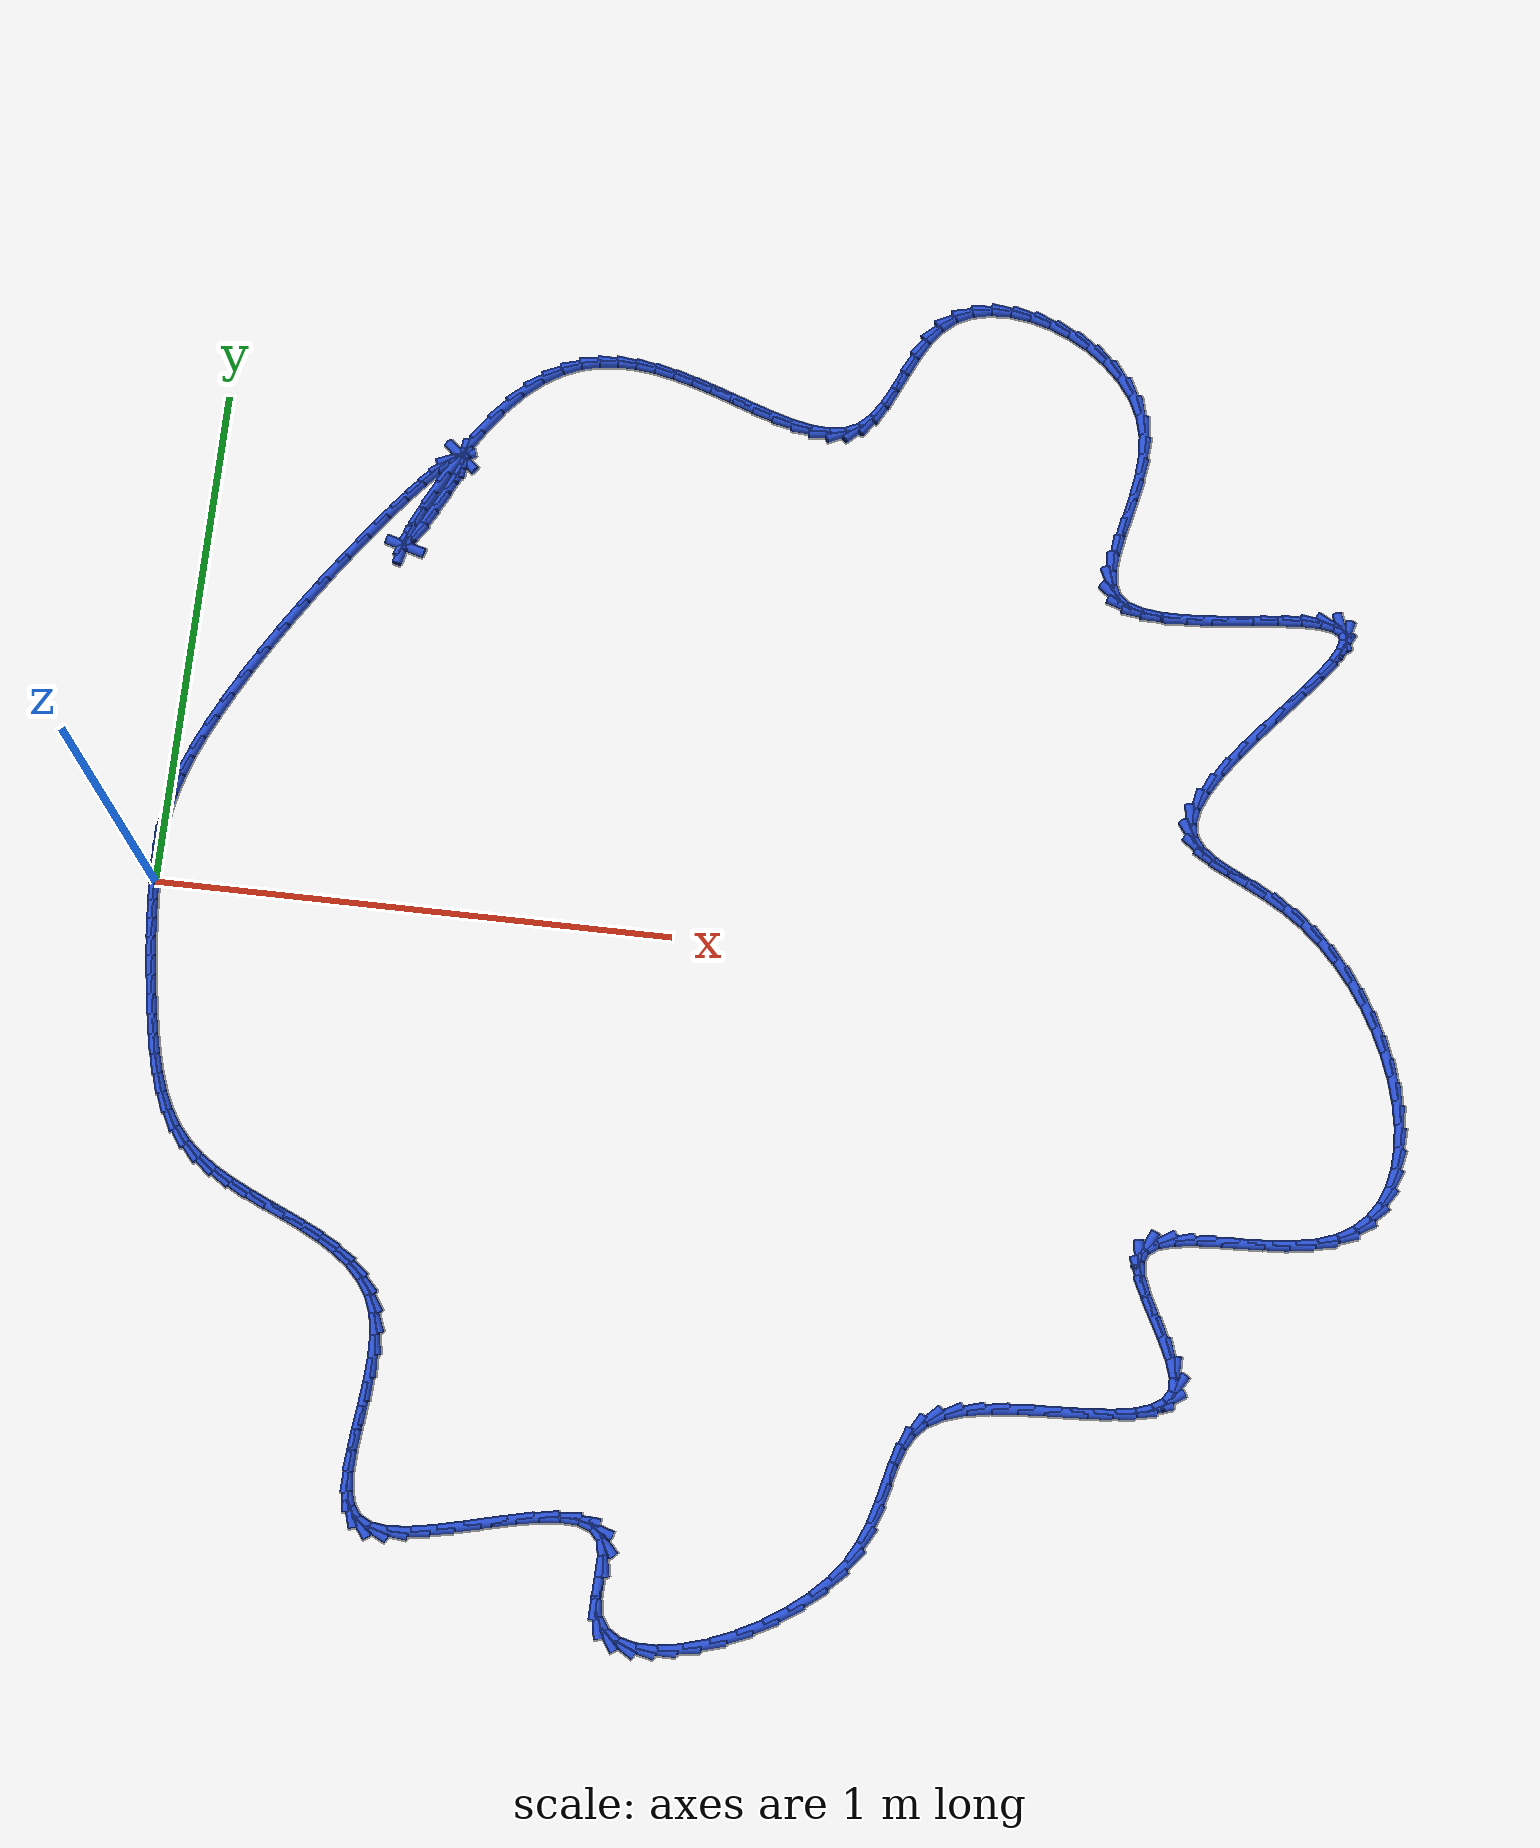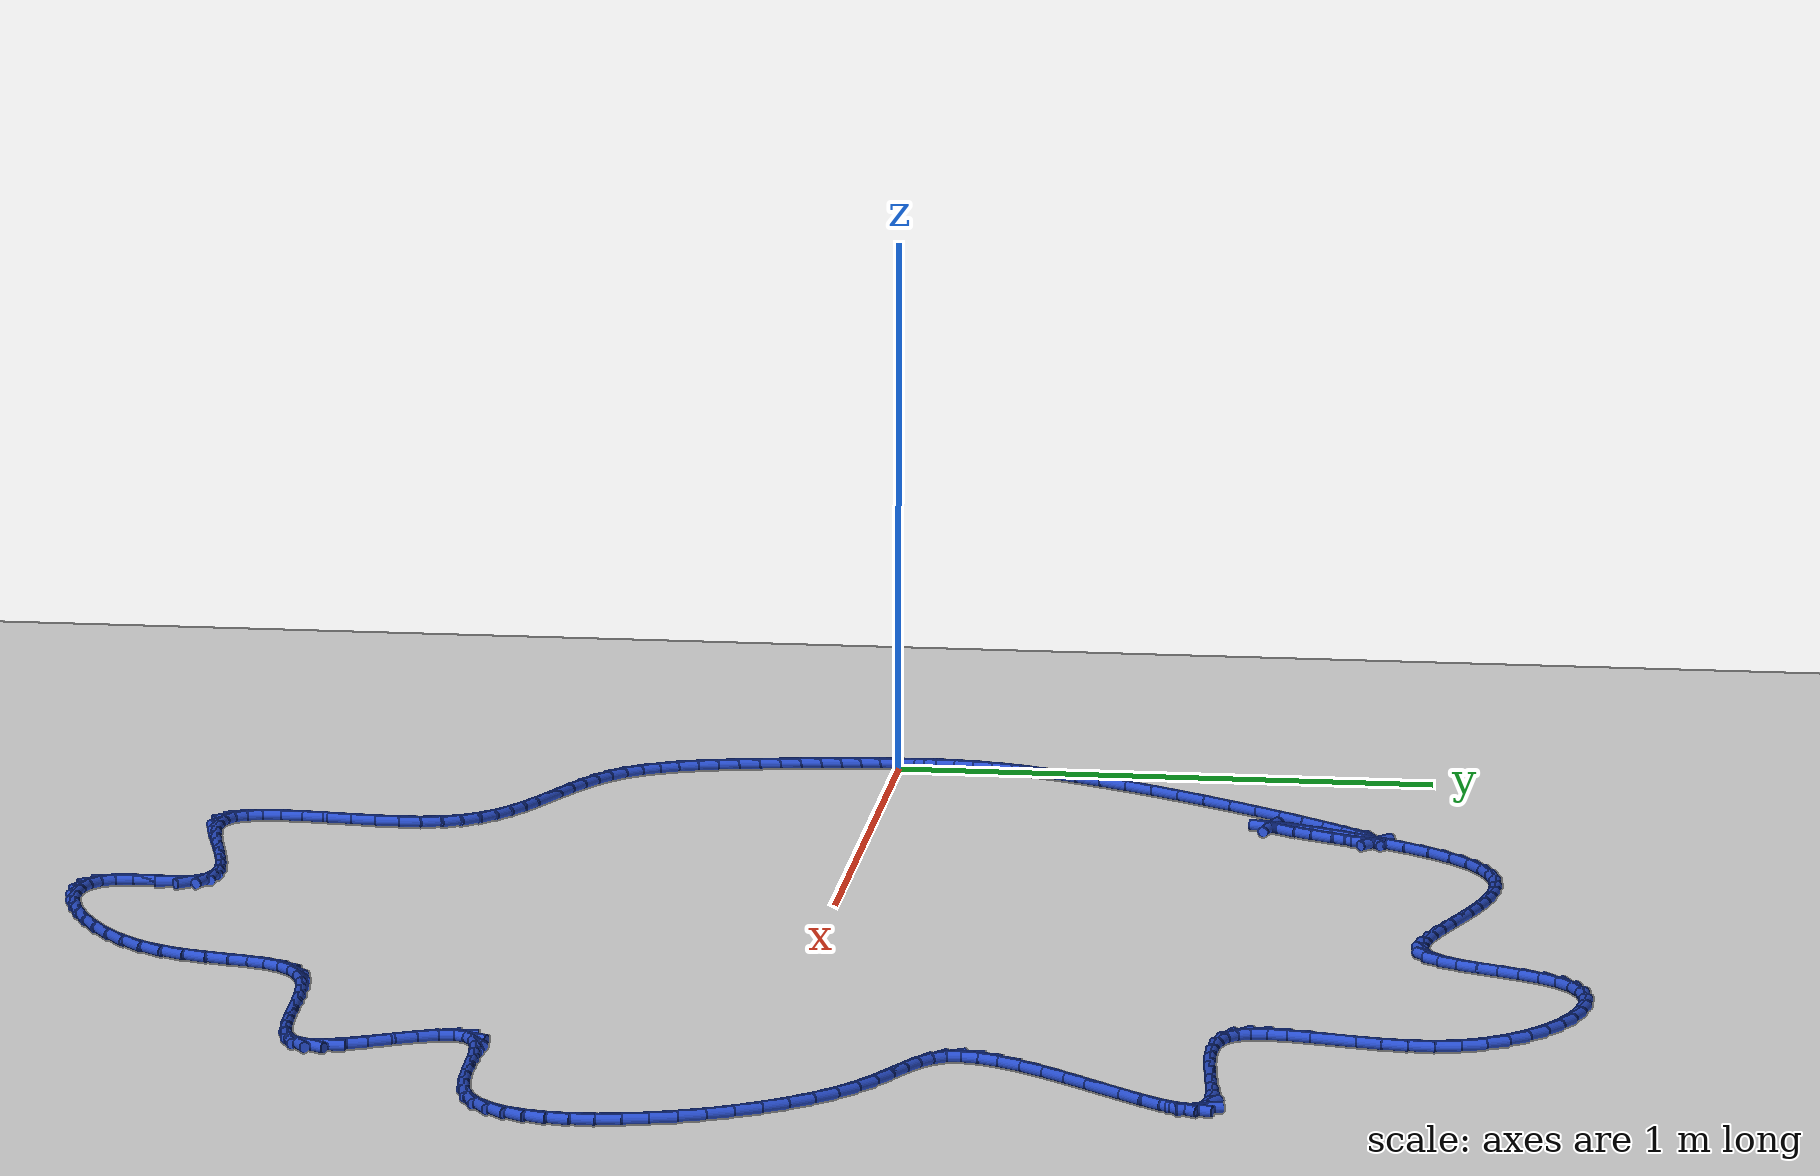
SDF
<sdf version="1.6">
 <world name="default">
  <light name="sun" type="directional">
   <pose>0 0 10 0 -0 0</pose>
   <diffuse>0.8 0.8 0.8 1</diffuse>
   <specular>0.2 0.2 0.2 1</specular>
   <attenuation>
    <range>1000</range>
    <constant>0.9</constant>
    <linear>0.01</linear>
    <quadratic>0.001</quadratic>
   </attenuation>
   <direction>-0.5 0.1 -0.9</direction>
  </light>
  <model name="ground_plane">
   <static>1</static>
   <link name="link">
    <collision name="collision">
     <geometry><plane><normal>0 0 1</normal><size>100 100</size></plane></geometry>
     <surface><friction><ode><mu>100</mu><mu2>50</mu2></ode></friction></surface>
    </collision>
    <visual name="visual">
     <cast_shadows>0</cast_shadows>
     <geometry><plane><normal>0 0 1</normal><size>100 100</size></plane></geometry>
     <material>
      <script><uri>file://media/materials/scripts/gazebo.material</uri><name>Gazebo/WhiteGlow</name></script>
     </material>
    </visual>
   </link>
  </model>
  <gravity>0 0 -9.8</gravity>
  <magnetic_field>6e-06 2.3e-05 -4.2e-05</magnetic_field>
  <atmosphere type="adiabatic"/>
  <physics name="default_physics" default="0" type="ode">
   <max_step_size>0.001</max_step_size>
   <real_time_factor>1</real_time_factor>
   <real_time_update_rate>1000</real_time_update_rate>
  </physics>
  <scene><ambient>0.4 0.4 0.4 1</ambient><background>0.7 0.7 0.7 1</background><shadows>1</shadows></scene>
  <spherical_coordinates>
   <surface_model>EARTH_WGS84</surface_model>
   <latitude_deg>0</latitude_deg>
   <longitude_deg>0</longitude_deg>
   <elevation>0</elevation>
   <heading_deg>0</heading_deg>
  </spherical_coordinates>
  <model name="line">
   <link name="link_0">
    <pose>2.0721814021629203e-17 4.163336342344337e-17 0.01 0 1.57 -1.5221960477817953</pose>
    <collision name="collision">
     <geometry><cylinder><radius>0.01</radius><length>0.08</length></cylinder></geometry>
    </collision>
    <visual name="visual">
     <material>
      <script><name>Gazebo/Blue</name><uri>file://media/materials/scripts/gazebo.material</uri></script>
     </material>
     <geometry><cylinder><radius>0.01</radius><length>0.08</length></cylinder></geometry>
    </visual>
   </link>
   <link name="link_1">
    <pose>-0.0016862516358424058 0.03466901478903752 0.01 0 1.57 -1.5606301533697617</pose>
    <collision name="collision">
     <geometry><cylinder><radius>0.01</radius><length>0.08</length></cylinder></geometry>
    </collision>
    <visual name="visual">
     <material>
      <script><name>Gazebo/Blue</name><uri>file://media/materials/scripts/gazebo.material</uri></script>
     </material>
     <geometry><cylinder><radius>0.01</radius><length>0.08</length></cylinder></geometry>
    </visual>
   </link>
   <link name="link_2">
    <pose>-0.0020366260753943615 0.06913255916225572 0.01 0 1.57 1.5277477523856136</pose>
    <collision name="collision">
     <geometry><cylinder><radius>0.01</radius><length>0.08</length></cylinder></geometry>
    </collision>
    <visual name="visual">
     <material>
      <script><name>Gazebo/Blue</name><uri>file://media/materials/scripts/gazebo.material</uri></script>
     </material>
     <geometry><cylinder><radius>0.01</radius><length>0.08</length></cylinder></geometry>
    </visual>
   </link>
   <link name="link_3">
    <pose>-0.0005349769415345087 0.10399367666121621 0.01 0 1.57 1.4633028487802766</pose>
    <collision name="collision">
     <geometry><cylinder><radius>0.01</radius><length>0.08</length></cylinder></geometry>
    </collision>
    <visual name="visual">
     <material>
      <script><name>Gazebo/Blue</name><uri>file://media/materials/scripts/gazebo.material</uri></script>
     </material>
     <geometry><cylinder><radius>0.01</radius><length>0.08</length></cylinder></geometry>
    </visual>
   </link>
   <link name="link_4">
    <pose>0.003334842142858487 0.13985541082748057 0.01 0 1.57 1.3924354433942654</pose>
    <collision name="collision">
     <geometry><cylinder><radius>0.01</radius><length>0.08</length></cylinder></geometry>
    </collision>
    <visual name="visual">
     <material>
      <script><name>Gazebo/Blue</name><uri>file://media/materials/scripts/gazebo.material</uri></script>
     </material>
     <geometry><cylinder><radius>0.01</radius><length>0.08</length></cylinder></geometry>
    </visual>
   </link>
   <link name="link_5">
    <pose>0.010088977554905957 0.1773208052026104 0.01 0 1.57 1.3202131406118476</pose>
    <collision name="collision">
     <geometry><cylinder><radius>0.01</radius><length>0.08</length></cylinder></geometry>
    </collision>
    <visual name="visual">
     <material>
      <script><name>Gazebo/Blue</name><uri>file://media/materials/scripts/gazebo.material</uri></script>
     </material>
     <geometry><cylinder><radius>0.01</radius><length>0.08</length></cylinder></geometry>
    </visual>
   </link>
   <link name="link_6">
    <pose>0.02024357567172924 0.21699290332816729 0.01 0 1.57 1.250941128274026</pose>
    <collision name="collision">
     <geometry><cylinder><radius>0.01</radius><length>0.08</length></cylinder></geometry>
    </collision>
    <visual name="visual">
     <material>
      <script><name>Gazebo/Blue</name><uri>file://media/materials/scripts/gazebo.material</uri></script>
     </material>
     <geometry><cylinder><radius>0.01</radius><length>0.08</length></cylinder></geometry>
    </visual>
   </link>
   <link name="link_7">
    <pose>0.034314782269369085 0.25947474802827686 0.01 0 1.57 1.1894129266577556</pose>
    <collision name="collision">
     <geometry><cylinder><radius>0.01</radius><length>0.08</length></cylinder></geometry>
    </collision>
    <visual name="visual">
     <material>
      <script><name>Gazebo/Blue</name><uri>file://media/materials/scripts/gazebo.material</uri></script>
     </material>
     <geometry><cylinder><radius>0.01</radius><length>0.08</length></cylinder></geometry>
    </visual>
   </link>
   <link name="link_8">
    <pose>0.05262808580988069 0.3051418179813442 0.01 0 1.57 1.1412424033178985</pose>
    <collision name="collision">
     <geometry><cylinder><radius>0.01</radius><length>0.08</length></cylinder></geometry>
    </collision>
    <visual name="visual">
     <material>
      <script><name>Gazebo/Blue</name><uri>file://media/materials/scripts/gazebo.material</uri></script>
     </material>
     <geometry><cylinder><radius>0.01</radius><length>0.08</length></cylinder></geometry>
    </visual>
   </link>
   <link name="link_9">
    <pose>0.07477963477600573 0.35349906859098795 0.01 0 1.57 1.1033511119911708</pose>
    <collision name="collision">
     <geometry><cylinder><radius>0.01</radius><length>0.08</length></cylinder></geometry>
    </collision>
    <visual name="visual">
     <material>
      <script><name>Gazebo/Blue</name><uri>file://media/materials/scripts/gazebo.material</uri></script>
     </material>
     <geometry><cylinder><radius>0.01</radius><length>0.08</length></cylinder></geometry>
    </visual>
   </link>
   <link name="link_10">
    <pose>0.10019120475483431 0.4038433278189455 0.01 0 1.57 1.0724564933578629</pose>
    <collision name="collision">
     <geometry><cylinder><radius>0.01</radius><length>0.08</length></cylinder></geometry>
    </collision>
    <visual name="visual">
     <material>
      <script><name>Gazebo/Blue</name><uri>file://media/materials/scripts/gazebo.material</uri></script>
     </material>
     <geometry><cylinder><radius>0.01</radius><length>0.08</length></cylinder></geometry>
    </visual>
   </link>
   <link name="link_11">
    <pose>0.1282845713334565 0.45547142362695414 0.01 0 1.57 1.0464193403920221</pose>
    <collision name="collision">
     <geometry><cylinder><radius>0.01</radius><length>0.08</length></cylinder></geometry>
    </collision>
    <visual name="visual">
     <material>
      <script><name>Gazebo/Blue</name><uri>file://media/materials/scripts/gazebo.material</uri></script>
     </material>
     <geometry><cylinder><radius>0.01</radius><length>0.08</length></cylinder></geometry>
    </visual>
   </link>
   <link name="link_12">
    <pose>0.15848151009896239 0.5076801839767512 0.01 0 1.57 1.0237608191480843</pose>
    <collision name="collision">
     <geometry><cylinder><radius>0.01</radius><length>0.08</length></cylinder></geometry>
    </collision>
    <visual name="visual">
     <material>
      <script><name>Gazebo/Blue</name><uri>file://media/materials/scripts/gazebo.material</uri></script>
     </material>
     <geometry><cylinder><radius>0.01</radius><length>0.08</length></cylinder></geometry>
    </visual>
   </link>
   <link name="link_13">
    <pose>0.19020379663844192 0.5597664368300735 0.01 0 1.57 1.0033864025507215</pose>
    <collision name="collision">
     <geometry><cylinder><radius>0.01</radius><length>0.08</length></cylinder></geometry>
    </collision>
    <visual name="visual">
     <material>
      <script><name>Gazebo/Blue</name><uri>file://media/materials/scripts/gazebo.material</uri></script>
     </material>
     <geometry><cylinder><radius>0.01</radius><length>0.08</length></cylinder></geometry>
    </visual>
   </link>
   <link name="link_14">
    <pose>0.22287320653898524 0.6110270101486587 0.01 0 1.57 0.9844126843384529</pose>
    <collision name="collision">
     <geometry><cylinder><radius>0.01</radius><length>0.08</length></cylinder></geometry>
    </collision>
    <visual name="visual">
     <material>
      <script><name>Gazebo/Blue</name><uri>file://media/materials/scripts/gazebo.material</uri></script>
     </material>
     <geometry><cylinder><radius>0.01</radius><length>0.08</length></cylinder></geometry>
    </visual>
   </link>
   <link name="link_15">
    <pose>0.2559115153876824 0.660758731894244 0.01 0 1.57 0.9660408560285011</pose>
    <collision name="collision">
     <geometry><cylinder><radius>0.01</radius><length>0.08</length></cylinder></geometry>
    </collision>
    <visual name="visual">
     <material>
      <script><name>Gazebo/Blue</name><uri>file://media/materials/scripts/gazebo.material</uri></script>
     </material>
     <geometry><cylinder><radius>0.01</radius><length>0.08</length></cylinder></geometry>
    </visual>
   </link>
   <link name="link_16">
    <pose>0.28874049877162355 0.7082584300285664 0.01 0 1.57 0.9474387387243113</pose>
    <collision name="collision">
     <geometry><cylinder><radius>0.01</radius><length>0.08</length></cylinder></geometry>
    </collision>
    <visual name="visual">
     <material>
      <script><name>Gazebo/Blue</name><uri>file://media/materials/scripts/gazebo.material</uri></script>
     </material>
     <geometry><cylinder><radius>0.01</radius><length>0.08</length></cylinder></geometry>
    </visual>
   </link>
   <link name="link_17">
    <pose>0.3207819322778985 0.752822932513363 0.01 0 1.57 0.9275914956249187</pose>
    <collision name="collision">
     <geometry><cylinder><radius>0.01</radius><length>0.08</length></cylinder></geometry>
    </collision>
    <visual name="visual">
     <material>
      <script><name>Gazebo/Blue</name><uri>file://media/materials/scripts/gazebo.material</uri></script>
     </material>
     <geometry><cylinder><radius>0.01</radius><length>0.08</length></cylinder></geometry>
    </visual>
   </link>
   <link name="link_18">
    <pose>0.35145759149359745 0.7937490673103714 0.01 0 1.57 0.9050532319355539</pose>
    <collision name="collision">
     <geometry><cylinder><radius>0.01</radius><length>0.08</length></cylinder></geometry>
    </collision>
    <visual name="visual">
     <material>
      <script><name>Gazebo/Blue</name><uri>file://media/materials/scripts/gazebo.material</uri></script>
     </material>
     <geometry><cylinder><radius>0.01</radius><length>0.08</length></cylinder></geometry>
    </visual>
   </link>
   <link name="link_19">
    <pose>0.38018925200581055 0.8303336623813288 0.01 0 1.57 0.8774405375104989</pose>
    <collision name="collision">
     <geometry><cylinder><radius>0.01</radius><length>0.08</length></cylinder></geometry>
    </collision>
    <visual name="visual">
     <material>
      <script><name>Gazebo/Blue</name><uri>file://media/materials/scripts/gazebo.material</uri></script>
     </material>
     <geometry><cylinder><radius>0.01</radius><length>0.08</length></cylinder></geometry>
    </visual>
   </link>
   <link name="link_20">
    <pose>0.4063986894016276 0.861873545687972 0.01 0 1.57 0.840209370832982</pose>
    <collision name="collision">
     <geometry><cylinder><radius>0.01</radius><length>0.08</length></cylinder></geometry>
    </collision>
    <visual name="visual">
     <material>
      <script><name>Gazebo/Blue</name><uri>file://media/materials/scripts/gazebo.material</uri></script>
     </material>
     <geometry><cylinder><radius>0.01</radius><length>0.08</length></cylinder></geometry>
    </visual>
   </link>
   <link name="link_21">
    <pose>0.42950767926813904 0.8876655451920389 0.01 0 1.57 0.7830929997503696</pose>
    <collision name="collision">
     <geometry><cylinder><radius>0.01</radius><length>0.08</length></cylinder></geometry>
    </collision>
    <visual name="visual">
     <material>
      <script><name>Gazebo/Blue</name><uri>file://media/materials/scripts/gazebo.material</uri></script>
     </material>
     <geometry><cylinder><radius>0.01</radius><length>0.08</length></cylinder></geometry>
    </visual>
   </link>
   <link name="link_22">
    <pose>0.44893799719243466 0.9070064888552665 0.01 0 1.57 0.6766660261103121</pose>
    <collision name="collision">
     <geometry><cylinder><radius>0.01</radius><length>0.08</length></cylinder></geometry>
    </collision>
    <visual name="visual">
     <material>
      <script><name>Gazebo/Blue</name><uri>file://media/materials/scripts/gazebo.material</uri></script>
     </material>
     <geometry><cylinder><radius>0.01</radius><length>0.08</length></cylinder></geometry>
    </visual>
   </link>
   <link name="link_23">
    <pose>0.46411141876160455 0.9191932046393917 0.01 0 1.57 0.3965774962460237</pose>
    <collision name="collision">
     <geometry><cylinder><radius>0.01</radius><length>0.08</length></cylinder></geometry>
    </collision>
    <visual name="visual">
     <material>
      <script><name>Gazebo/Blue</name><uri>file://media/materials/scripts/gazebo.material</uri></script>
     </material>
     <geometry><cylinder><radius>0.01</radius><length>0.08</length></cylinder></geometry>
    </visual>
   </link>
   <link name="link_24">
    <pose>0.47444971956273885 0.9235225205061519 0.01 0 1.57 -0.7097799023059139</pose>
    <collision name="collision">
     <geometry><cylinder><radius>0.01</radius><length>0.08</length></cylinder></geometry>
    </collision>
    <visual name="visual">
     <material>
      <script><name>Gazebo/Blue</name><uri>file://media/materials/scripts/gazebo.material</uri></script>
     </material>
     <geometry><cylinder><radius>0.01</radius><length>0.08</length></cylinder></geometry>
    </visual>
   </link>
   <link name="link_25">
    <pose>0.47937467518292737 0.9192912644172844 0.01 0 1.57 1.4919225792418223</pose>
    <collision name="collision">
     <geometry><cylinder><radius>0.01</radius><length>0.08</length></cylinder></geometry>
    </collision>
    <visual name="visual">
     <material>
      <script><name>Gazebo/Blue</name><uri>file://media/materials/scripts/gazebo.material</uri></script>
     </material>
     <geometry><cylinder><radius>0.01</radius><length>0.08</length></cylinder></geometry>
    </visual>
   </link>
   <link name="link_26">
    <pose>0.4783080612092605 0.9057962643345265 0.01 0 1.57 1.2561294388235926</pose>
    <collision name="collision">
     <geometry><cylinder><radius>0.01</radius><length>0.08</length></cylinder></geometry>
    </collision>
    <visual name="visual">
     <material>
      <script><name>Gazebo/Blue</name><uri>file://media/materials/scripts/gazebo.material</uri></script>
     </material>
     <geometry><cylinder><radius>0.01</radius><length>0.08</length></cylinder></geometry>
    </visual>
   </link>
   <link name="link_27">
    <pose>0.4706716532288282 0.8823343482196155 0.01 0 1.57 1.1640334516660944</pose>
    <collision name="collision">
     <geometry><cylinder><radius>0.01</radius><length>0.08</length></cylinder></geometry>
    </collision>
    <visual name="visual">
     <material>
      <script><name>Gazebo/Blue</name><uri>file://media/materials/scripts/gazebo.material</uri></script>
     </material>
     <geometry><cylinder><radius>0.01</radius><length>0.08</length></cylinder></geometry>
    </visual>
   </link>
   <link name="link_28">
    <pose>0.4562442401005578 0.8488435958315781 0.01 0 1.57 1.1198259371495412</pose>
    <collision name="collision">
     <geometry><cylinder><radius>0.01</radius><length>0.08</length></cylinder></geometry>
    </collision>
    <visual name="visual">
     <material>
      <script><name>Gazebo/Blue</name><uri>file://media/materials/scripts/gazebo.material</uri></script>
     </material>
     <geometry><cylinder><radius>0.01</radius><length>0.08</length></cylinder></geometry>
    </visual>
   </link>
   <link name="link_29">
    <pose>0.43737880218477027 0.8098857383649793 0.01 0 1.57 1.088221807217513</pose>
    <collision name="collision">
     <geometry><cylinder><radius>0.01</radius><length>0.08</length></cylinder></geometry>
    </collision>
    <visual name="visual">
     <material>
      <script><name>Gazebo/Blue</name><uri>file://media/materials/scripts/gazebo.material</uri></script>
     </material>
     <geometry><cylinder><radius>0.01</radius><length>0.08</length></cylinder></geometry>
    </visual>
   </link>
   <link name="link_30">
    <pose>0.4175573684938185 0.7720504553694052 0.01 0 1.57 1.0495907408312326</pose>
    <collision name="collision">
     <geometry><cylinder><radius>0.01</radius><length>0.08</length></cylinder></geometry>
    </collision>
    <visual name="visual">
     <material>
      <script><name>Gazebo/Blue</name><uri>file://media/materials/scripts/gazebo.material</uri></script>
     </material>
     <geometry><cylinder><radius>0.01</radius><length>0.08</length></cylinder></geometry>
    </visual>
   </link>
   <link name="link_31">
    <pose>0.40026678510043573 0.7419360785899481 0.01 0 1.57 0.9519673105431965</pose>
    <collision name="collision">
     <geometry><cylinder><radius>0.01</radius><length>0.08</length></cylinder></geometry>
    </collision>
    <visual name="visual">
     <material>
      <script><name>Gazebo/Blue</name><uri>file://media/materials/scripts/gazebo.material</uri></script>
     </material>
     <geometry><cylinder><radius>0.01</radius><length>0.08</length></cylinder></geometry>
    </visual>
   </link>
   <link name="link_32">
    <pose>0.38894983859831506 0.726044675515083 0.01 0 1.57 -0.2719744744640523</pose>
    <collision name="collision">
     <geometry><cylinder><radius>0.01</radius><length>0.08</length></cylinder></geometry>
    </collision>
    <visual name="visual">
     <material>
      <script><name>Gazebo/Blue</name><uri>file://media/materials/scripts/gazebo.material</uri></script>
     </material>
     <geometry><cylinder><radius>0.01</radius><length>0.08</length></cylinder></geometry>
    </visual>
   </link>
   <link name="link_33">
    <pose>0.38530254700189565 0.7270618504696597 0.01 0 1.57 1.3545416241763109</pose>
    <collision name="collision">
     <geometry><cylinder><radius>0.01</radius><length>0.08</length></cylinder></geometry>
    </collision>
    <visual name="visual">
     <material>
      <script><name>Gazebo/Blue</name><uri>file://media/materials/scripts/gazebo.material</uri></script>
     </material>
     <geometry><cylinder><radius>0.01</radius><length>0.08</length></cylinder></geometry>
    </visual>
   </link>
   <link name="link_34">
    <pose>0.3887319720929825 0.7426721347979673 0.01 0 1.57 1.2303765464891425</pose>
    <collision name="collision">
     <geometry><cylinder><radius>0.01</radius><length>0.08</length></cylinder></geometry>
    </collision>
    <visual name="visual">
     <material>
      <script><name>Gazebo/Blue</name><uri>file://media/materials/scripts/gazebo.material</uri></script>
     </material>
     <geometry><cylinder><radius>0.01</radius><length>0.08</length></cylinder></geometry>
    </visual>
   </link>
   <link name="link_35">
    <pose>0.39849018847131423 0.7702214329201479 0.01 0 1.57 1.1762020324536666</pose>
    <collision name="collision">
     <geometry><cylinder><radius>0.01</radius><length>0.08</length></cylinder></geometry>
    </collision>
    <visual name="visual">
     <material>
      <script><name>Gazebo/Blue</name><uri>file://media/materials/scripts/gazebo.material</uri></script>
     </material>
     <geometry><cylinder><radius>0.01</radius><length>0.08</length></cylinder></geometry>
    </visual>
   </link>
   <link name="link_36">
    <pose>0.4138292707366294 0.8070556492563422 0.01 0 1.57 1.136280830870113</pose>
    <collision name="collision">
     <geometry><cylinder><radius>0.01</radius><length>0.08</length></cylinder></geometry>
    </collision>
    <visual name="visual">
     <material>
      <script><name>Gazebo/Blue</name><uri>file://media/materials/scripts/gazebo.material</uri></script>
     </material>
     <geometry><cylinder><radius>0.01</radius><length>0.08</length></cylinder></geometry>
    </visual>
   </link>
   <link name="link_37">
    <pose>0.4340012934886664 0.8505206882266921 0.01 0 1.57 1.0981485871081271</pose>
    <collision name="collision">
     <geometry><cylinder><radius>0.01</radius><length>0.08</length></cylinder></geometry>
    </collision>
    <visual name="visual">
     <material>
      <script><name>Gazebo/Blue</name><uri>file://media/materials/scripts/gazebo.material</uri></script>
     </material>
     <geometry><cylinder><radius>0.01</radius><length>0.08</length></cylinder></geometry>
    </visual>
   </link>
   <link name="link_38">
    <pose>0.458258331327164 0.8979624542513392 0.01 0 1.57 1.0558533815253084</pose>
    <collision name="collision">
     <geometry><cylinder><radius>0.01</radius><length>0.08</length></cylinder></geometry>
    </collision>
    <visual name="visual">
     <material>
      <script><name>Gazebo/Blue</name><uri>file://media/materials/scripts/gazebo.material</uri></script>
     </material>
     <geometry><cylinder><radius>0.01</radius><length>0.08</length></cylinder></geometry>
    </visual>
   </link>
   <link name="link_39">
    <pose>0.4858524588518607 0.946726851750425 0.01 0 1.57 1.0040866494532676</pose>
    <collision name="collision">
     <geometry><cylinder><radius>0.01</radius><length>0.08</length></cylinder></geometry>
    </collision>
    <visual name="visual">
     <material>
      <script><name>Gazebo/Blue</name><uri>file://media/materials/scripts/gazebo.material</uri></script>
     </material>
     <geometry><cylinder><radius>0.01</radius><length>0.08</length></cylinder></geometry>
    </visual>
   </link>
   <link name="link_40">
    <pose>0.516035750662495 0.9941597851440909 0.01 0 1.57 0.9356103478978652</pose>
    <collision name="collision">
     <geometry><cylinder><radius>0.01</radius><length>0.08</length></cylinder></geometry>
    </collision>
    <visual name="visual">
     <material>
      <script><name>Gazebo/Blue</name><uri>file://media/materials/scripts/gazebo.material</uri></script>
     </material>
     <geometry><cylinder><radius>0.01</radius><length>0.08</length></cylinder></geometry>
    </visual>
   </link>
   <link name="link_41">
    <pose>0.5480602813588054 1.0376071588524782 0.01 0 1.57 0.8385921787919395</pose>
    <collision name="collision">
     <geometry><cylinder><radius>0.01</radius><length>0.08</length></cylinder></geometry>
    </collision>
    <visual name="visual">
     <material>
      <script><name>Gazebo/Blue</name><uri>file://media/materials/scripts/gazebo.material</uri></script>
     </material>
     <geometry><cylinder><radius>0.01</radius><length>0.08</length></cylinder></geometry>
    </visual>
   </link>
   <link name="link_42">
    <pose>0.5811889219782671 1.074462018076603 0.01 0 1.57 0.7105581301492536</pose>
    <collision name="collision">
     <geometry><cylinder><radius>0.01</radius><length>0.08</length></cylinder></geometry>
    </collision>
    <visual name="visual">
     <material>
      <script><name>Gazebo/Blue</name><uri>file://media/materials/scripts/gazebo.material</uri></script>
     </material>
     <geometry><cylinder><radius>0.01</radius><length>0.08</length></cylinder></geometry>
    </visual>
   </link>
   <link name="link_43">
    <pose>0.6150175830558817 1.1035715674687974 0.01 0 1.57 0.5655733959831735</pose>
    <collision name="collision">
     <geometry><cylinder><radius>0.01</radius><length>0.08</length></cylinder></geometry>
    </collision>
    <visual name="visual">
     <material>
      <script><name>Gazebo/Blue</name><uri>file://media/materials/scripts/gazebo.material</uri></script>
     </material>
     <geometry><cylinder><radius>0.01</radius><length>0.08</length></cylinder></geometry>
    </visual>
   </link>
   <link name="link_44">
    <pose>0.6495304367287406 1.1254782889156494 0.01 0 1.57 0.41099620286412136</pose>
    <collision name="collision">
     <geometry><cylinder><radius>0.01</radius><length>0.08</length></cylinder></geometry>
    </collision>
    <visual name="visual">
     <material>
      <script><name>Gazebo/Blue</name><uri>file://media/materials/scripts/gazebo.material</uri></script>
     </material>
     <geometry><cylinder><radius>0.01</radius><length>0.08</length></cylinder></geometry>
    </visual>
   </link>
   <link name="link_45">
    <pose>0.6847335775464717 1.1408203847321674 0.01 0 1.57 0.2565010872065976</pose>
    <collision name="collision">
     <geometry><cylinder><radius>0.01</radius><length>0.08</length></cylinder></geometry>
    </collision>
    <visual name="visual">
     <material>
      <script><name>Gazebo/Blue</name><uri>file://media/materials/scripts/gazebo.material</uri></script>
     </material>
     <geometry><cylinder><radius>0.01</radius><length>0.08</length></cylinder></geometry>
    </visual>
   </link>
   <link name="link_46">
    <pose>0.7206331000587022 1.1502360572333612 0.01 0 1.57 0.11229137412723873</pose>
    <collision name="collision">
     <geometry><cylinder><radius>0.01</radius><length>0.08</length></cylinder></geometry>
    </collision>
    <visual name="visual">
     <material>
      <script><name>Gazebo/Blue</name><uri>file://media/materials/scripts/gazebo.material</uri></script>
     </material>
     <geometry><cylinder><radius>0.01</radius><length>0.08</length></cylinder></geometry>
    </visual>
   </link>
   <link name="link_47">
    <pose>0.7572350988150601 1.1543635087342392 0.01 0 1.57 -0.014004959587400417</pose>
    <collision name="collision">
     <geometry><cylinder><radius>0.01</radius><length>0.08</length></cylinder></geometry>
    </collision>
    <visual name="visual">
     <material>
      <script><name>Gazebo/Blue</name><uri>file://media/materials/scripts/gazebo.material</uri></script>
     </material>
     <geometry><cylinder><radius>0.01</radius><length>0.08</length></cylinder></geometry>
    </visual>
   </link>
   <link name="link_48">
    <pose>0.7945456683651727 1.1538409415498105 0.01 0 1.57 -0.1186862477228279</pose>
    <collision name="collision">
     <geometry><cylinder><radius>0.01</radius><length>0.08</length></cylinder></geometry>
    </collision>
    <visual name="visual">
     <material>
      <script><name>Gazebo/Blue</name><uri>file://media/materials/scripts/gazebo.material</uri></script>
     </material>
     <geometry><cylinder><radius>0.01</radius><length>0.08</length></cylinder></geometry>
    </visual>
   </link>
   <link name="link_49">
    <pose>0.8325709032586673 1.1493065579950847 0.01 0 1.57 -0.20133325647392575</pose>
    <collision name="collision">
     <geometry><cylinder><radius>0.01</radius><length>0.08</length></cylinder></geometry>
    </collision>
    <visual name="visual">
     <material>
      <script><name>Gazebo/Blue</name><uri>file://media/materials/scripts/gazebo.material</uri></script>
     </material>
     <geometry><cylinder><radius>0.01</radius><length>0.08</length></cylinder></geometry>
    </visual>
   </link>
   <link name="link_50">
    <pose>0.8713168980451721 1.14139856038507 0.01 0 1.57 -0.2633750907515432</pose>
    <collision name="collision">
     <geometry><cylinder><radius>0.01</radius><length>0.08</length></cylinder></geometry>
    </collision>
    <visual name="visual">
     <material>
      <script><name>Gazebo/Blue</name><uri>file://media/materials/scripts/gazebo.material</uri></script>
     </material>
     <geometry><cylinder><radius>0.01</radius><length>0.08</length></cylinder></geometry>
    </visual>
   </link>
   <link name="link_51">
    <pose>0.910789747274314 1.130755151034776 0.01 0 1.57 -0.30687484125945513</pose>
    <collision name="collision">
     <geometry><cylinder><radius>0.01</radius><length>0.08</length></cylinder></geometry>
    </collision>
    <visual name="visual">
     <material>
      <script><name>Gazebo/Blue</name><uri>file://media/materials/scripts/gazebo.material</uri></script>
     </material>
     <geometry><cylinder><radius>0.01</radius><length>0.08</length></cylinder></geometry>
    </visual>
   </link>
   <link name="link_52">
    <pose>0.9509955454957211 1.1180145322592112 0.01 0 1.57 -0.3338180950539624</pose>
    <collision name="collision">
     <geometry><cylinder><radius>0.01</radius><length>0.08</length></cylinder></geometry>
    </collision>
    <visual name="visual">
     <material>
      <script><name>Gazebo/Blue</name><uri>file://media/materials/scripts/gazebo.material</uri></script>
     </material>
     <geometry><cylinder><radius>0.01</radius><length>0.08</length></cylinder></geometry>
    </visual>
   </link>
   <link name="link_53">
    <pose>0.991940250162675 1.103815051117857 0.01 0 1.57 -0.34305378490728666</pose>
    <collision name="collision">
     <geometry><cylinder><radius>0.01</radius><length>0.08</length></cylinder></geometry>
    </collision>
    <visual name="visual">
     <material>
      <script><name>Gazebo/Blue</name><uri>file://media/materials/scripts/gazebo.material</uri></script>
     </material>
     <geometry><cylinder><radius>0.01</radius><length>0.08</length></cylinder></geometry>
    </visual>
   </link>
   <link name="link_54">
    <pose>1.0334445051789358 1.0889907062156663 0.01 0 1.57 -0.3272957050151631</pose>
    <collision name="collision">
     <geometry><cylinder><radius>0.01</radius><length>0.08</length></cylinder></geometry>
    </collision>
    <visual name="visual">
     <material>
      <script><name>Gazebo/Blue</name><uri>file://media/materials/scripts/gazebo.material</uri></script>
     </material>
     <geometry><cylinder><radius>0.01</radius><length>0.08</length></cylinder></geometry>
    </visual>
   </link>
   <link name="link_55">
    <pose>1.0747772366231614 1.07495799239397 0.01 0 1.57 -0.2827508466270067</pose>
    <collision name="collision">
     <geometry><cylinder><radius>0.01</radius><length>0.08</length></cylinder></geometry>
    </collision>
    <visual name="visual">
     <material>
      <script><name>Gazebo/Blue</name><uri>file://media/materials/scripts/gazebo.material</uri></script>
     </material>
     <geometry><cylinder><radius>0.01</radius><length>0.08</length></cylinder></geometry>
    </visual>
   </link>
   <link name="link_56">
    <pose>1.1151051571162207 1.0632413200838426 0.01 0 1.57 -0.20184469161221588</pose>
    <collision name="collision">
     <geometry><cylinder><radius>0.01</radius><length>0.08</length></cylinder></geometry>
    </collision>
    <visual name="visual">
     <material>
      <script><name>Gazebo/Blue</name><uri>file://media/materials/scripts/gazebo.material</uri></script>
     </material>
     <geometry><cylinder><radius>0.01</radius><length>0.08</length></cylinder></geometry>
    </visual>
   </link>
   <link name="link_57">
    <pose>1.1535949792789832 1.0553650997163582 0.01 0 1.57 -0.06999900424213847</pose>
    <collision name="collision">
     <geometry><cylinder><radius>0.01</radius><length>0.08</length></cylinder></geometry>
    </collision>
    <visual name="visual">
     <material>
      <script><name>Gazebo/Blue</name><uri>file://media/materials/scripts/gazebo.material</uri></script>
     </material>
     <geometry><cylinder><radius>0.01</radius><length>0.08</length></cylinder></geometry>
    </visual>
   </link>
   <link name="link_58">
    <pose>1.1894134157323186 1.0528537417225916 0.01 0 1.57 0.13466150895083281</pose>
    <collision name="collision">
     <geometry><cylinder><radius>0.01</radius><length>0.08</length></cylinder></geometry>
    </collision>
    <visual name="visual">
     <material>
      <script><name>Gazebo/Blue</name><uri>file://media/materials/scripts/gazebo.material</uri></script>
     </material>
     <geometry><cylinder><radius>0.01</radius><length>0.08</length></cylinder></geometry>
    </visual>
   </link>
   <link name="link_59">
    <pose>1.2217271790970958 1.057231656533618 0.01 0 1.57 0.4288456730193809</pose>
    <collision name="collision">
     <geometry><cylinder><radius>0.01</radius><length>0.08</length></cylinder></geometry>
    </collision>
    <visual name="visual">
     <material>
      <script><name>Gazebo/Blue</name><uri>file://media/materials/scripts/gazebo.material</uri></script>
     </material>
     <geometry><cylinder><radius>0.01</radius><length>0.08</length></cylinder></geometry>
    </visual>
   </link>
   <link name="link_60">
    <pose>1.2497031522457636 1.070022960835237 0.01 0 1.57 0.7557472335822882</pose>
    <collision name="collision">
     <geometry><cylinder><radius>0.01</radius><length>0.08</length></cylinder></geometry>
    </collision>
    <visual name="visual">
     <material>
      <script><name>Gazebo/Blue</name><uri>file://media/materials/scripts/gazebo.material</uri></script>
     </material>
     <geometry><cylinder><radius>0.01</radius><length>0.08</length></cylinder></geometry>
    </visual>
   </link>
   <link name="link_61">
    <pose>1.2729721134688545 1.0919513846858242 0.01 0 1.57 0.9787714327131343</pose>
    <collision name="collision">
     <geometry><cylinder><radius>0.01</radius><length>0.08</length></cylinder></geometry>
    </collision>
    <visual name="visual">
     <material>
      <script><name>Gazebo/Blue</name><uri>file://media/materials/scripts/gazebo.material</uri></script>
     </material>
     <geometry><cylinder><radius>0.01</radius><length>0.08</length></cylinder></geometry>
    </visual>
   </link>
   <link name="link_62">
    <pose>1.2926393245220775 1.1211966432604923 0.01 0 1.57 1.0991370596460108</pose>
    <collision name="collision">
     <geometry><cylinder><radius>0.01</radius><length>0.08</length></cylinder></geometry>
    </collision>
    <visual name="visual">
     <material>
      <script><name>Gazebo/Blue</name><uri>file://media/materials/scripts/gazebo.material</uri></script>
     </material>
     <geometry><cylinder><radius>0.01</radius><length>0.08</length></cylinder></geometry>
    </visual>
   </link>
   <link name="link_63">
    <pose>1.310102336750312 1.1554341469505882 0.01 0 1.57 1.146837839591366</pose>
    <collision name="collision">
     <geometry><cylinder><radius>0.01</radius><length>0.08</length></cylinder></geometry>
    </collision>
    <visual name="visual">
     <material>
      <script><name>Gazebo/Blue</name><uri>file://media/materials/scripts/gazebo.material</uri></script>
     </material>
     <geometry><cylinder><radius>0.01</radius><length>0.08</length></cylinder></geometry>
    </visual>
   </link>
   <link name="link_64">
    <pose>1.3267587014984363 1.1923393061474576 0.01 0 1.57 1.1371547107826017</pose>
    <collision name="collision">
     <geometry><cylinder><radius>0.01</radius><length>0.08</length></cylinder></geometry>
    </collision>
    <visual name="visual">
     <material>
      <script><name>Gazebo/Blue</name><uri>file://media/materials/scripts/gazebo.material</uri></script>
     </material>
     <geometry><cylinder><radius>0.01</radius><length>0.08</length></cylinder></geometry>
    </visual>
   </link>
   <link name="link_65">
    <pose>1.3440059701113316 1.2295875312424476 0.01 0 1.57 1.071464001234181</pose>
    <collision name="collision">
     <geometry><cylinder><radius>0.01</radius><length>0.08</length></cylinder></geometry>
    </collision>
    <visual name="visual">
     <material>
      <script><name>Gazebo/Blue</name><uri>file://media/materials/scripts/gazebo.material</uri></script>
     </material>
     <geometry><cylinder><radius>0.01</radius><length>0.08</length></cylinder></geometry>
    </visual>
   </link>
   <link name="link_66">
    <pose>1.363241693933876 1.2648542326269046 0.01 0 1.57 0.9397867354541178</pose>
    <collision name="collision">
     <geometry><cylinder><radius>0.01</radius><length>0.08</length></cylinder></geometry>
    </collision>
    <visual name="visual">
     <material>
      <script><name>Gazebo/Blue</name><uri>file://media/materials/scripts/gazebo.material</uri></script>
     </material>
     <geometry><cylinder><radius>0.01</radius><length>0.08</length></cylinder></geometry>
    </visual>
   </link>
   <link name="link_67">
    <pose>1.3858634243109487 1.2958148206921742 0.01 0 1.57 0.7262623180877601</pose>
    <collision name="collision">
     <geometry><cylinder><radius>0.01</radius><length>0.08</length></cylinder></geometry>
    </collision>
    <visual name="visual">
     <material>
      <script><name>Gazebo/Blue</name><uri>file://media/materials/scripts/gazebo.material</uri></script>
     </material>
     <geometry><cylinder><radius>0.01</radius><length>0.08</length></cylinder></geometry>
    </visual>
   </link>
   <link name="link_68">
    <pose>1.4132626971803164 1.3201510968237151 0.01 0 1.57 0.46096076140459136</pose>
    <collision name="collision">
     <geometry><cylinder><radius>0.01</radius><length>0.08</length></cylinder></geometry>
    </collision>
    <visual name="visual">
     <material>
      <script><name>Gazebo/Blue</name><uri>file://media/materials/scripts/gazebo.material</uri></script>
     </material>
     <geometry><cylinder><radius>0.01</radius><length>0.08</length></cylinder></geometry>
    </visual>
   </link>
   <link name="link_69">
    <pose>1.4460114517132718 1.3364156327488494 0.01 0 1.57 0.22544161819047126</pose>
    <collision name="collision">
     <geometry><cylinder><radius>0.01</radius><length>0.08</length></cylinder></geometry>
    </collision>
    <visual name="visual">
     <material>
      <script><name>Gazebo/Blue</name><uri>file://media/materials/scripts/gazebo.material</uri></script>
     </material>
     <geometry><cylinder><radius>0.01</radius><length>0.08</length></cylinder></geometry>
    </visual>
   </link>
   <link name="link_70">
    <pose>1.4830379563795635 1.3449072975904528 0.01 0 1.57 0.030618090259909747</pose>
    <collision name="collision">
     <geometry><cylinder><radius>0.01</radius><length>0.08</length></cylinder></geometry>
    </collision>
    <visual name="visual">
     <material>
      <script><name>Gazebo/Blue</name><uri>file://media/materials/scripts/gazebo.material</uri></script>
     </material>
     <geometry><cylinder><radius>0.01</radius><length>0.08</length></cylinder></geometry>
    </visual>
   </link>
   <link name="link_71">
    <pose>1.5230741828160899 1.346133513588298 0.01 0 1.57 -0.13164412909860207</pose>
    <collision name="collision">
     <geometry><cylinder><radius>0.01</radius><length>0.08</length></cylinder></geometry>
    </collision>
    <visual name="visual">
     <material>
      <script><name>Gazebo/Blue</name><uri>file://media/materials/scripts/gazebo.material</uri></script>
     </material>
     <geometry><cylinder><radius>0.01</radius><length>0.08</length></cylinder></geometry>
    </visual>
   </link>
   <link name="link_72">
    <pose>1.5648521026597506 1.3406017029821578 0.01 0 1.57 -0.27195429950035854</pose>
    <collision name="collision">
     <geometry><cylinder><radius>0.01</radius><length>0.08</length></cylinder></geometry>
    </collision>
    <visual name="visual">
     <material>
      <script><name>Gazebo/Blue</name><uri>file://media/materials/scripts/gazebo.material</uri></script>
     </material>
     <geometry><cylinder><radius>0.01</radius><length>0.08</length></cylinder></geometry>
    </visual>
   </link>
   <link name="link_73">
    <pose>1.6071036875474451 1.328819288011805 0.01 0 1.57 -0.3999542624763496</pose>
    <collision name="collision">
     <geometry><cylinder><radius>0.01</radius><length>0.08</length></cylinder></geometry>
    </collision>
    <visual name="visual">
     <material>
      <script><name>Gazebo/Blue</name><uri>file://media/materials/scripts/gazebo.material</uri></script>
     </material>
     <geometry><cylinder><radius>0.01</radius><length>0.08</length></cylinder></geometry>
    </visual>
   </link>
   <link name="link_74">
    <pose>1.6485609091160724 1.3112936909170114 0.01 0 1.57 -0.5239174390987342</pose>
    <collision name="collision">
     <geometry><cylinder><radius>0.01</radius><length>0.08</length></cylinder></geometry>
    </collision>
    <visual name="visual">
     <material>
      <script><name>Gazebo/Blue</name><uri>file://media/materials/scripts/gazebo.material</uri></script>
     </material>
     <geometry><cylinder><radius>0.01</radius><length>0.08</length></cylinder></geometry>
    </visual>
   </link>
   <link name="link_75">
    <pose>1.6879557390025315 1.2885323339375512 0.01 0 1.57 -0.6512880748055878</pose>
    <collision name="collision">
     <geometry><cylinder><radius>0.01</radius><length>0.08</length></cylinder></geometry>
    </collision>
    <visual name="visual">
     <material>
      <script><name>Gazebo/Blue</name><uri>file://media/materials/scripts/gazebo.material</uri></script>
     </material>
     <geometry><cylinder><radius>0.01</radius><length>0.08</length></cylinder></geometry>
    </visual>
   </link>
   <link name="link_76">
    <pose>1.7240201488437221 1.2610426393131962 0.01 0 1.57 -0.7892706016778485</pose>
    <collision name="collision">
     <geometry><cylinder><radius>0.01</radius><length>0.08</length></cylinder></geometry>
    </collision>
    <visual name="visual">
     <material>
      <script><name>Gazebo/Blue</name><uri>file://media/materials/scripts/gazebo.material</uri></script>
     </material>
     <geometry><cylinder><radius>0.01</radius><length>0.08</length></cylinder></geometry>
    </visual>
   </link>
   <link name="link_77">
    <pose>1.7554861102765438 1.2293320292837195 0.01 0 1.57 -0.9450254512287154</pose>
    <collision name="collision">
     <geometry><cylinder><radius>0.01</radius><length>0.08</length></cylinder></geometry>
    </collision>
    <visual name="visual">
     <material>
      <script><name>Gazebo/Blue</name><uri>file://media/materials/scripts/gazebo.material</uri></script>
     </material>
     <geometry><cylinder><radius>0.01</radius><length>0.08</length></cylinder></geometry>
    </visual>
   </link>
   <link name="link_78">
    <pose>1.7810855949378952 1.1939079260888925 0.01 0 1.57 -1.1249082423948167</pose>
    <collision name="collision">
     <geometry><cylinder><radius>0.01</radius><length>0.08</length></cylinder></geometry>
    </collision>
    <visual name="visual">
     <material>
      <script><name>Gazebo/Blue</name><uri>file://media/materials/scripts/gazebo.material</uri></script>
     </material>
     <geometry><cylinder><radius>0.01</radius><length>0.08</length></cylinder></geometry>
    </visual>
   </link>
   <link name="link_79">
    <pose>1.7995505744646758 1.1552777519684896 0.01 0 1.57 -1.3299193650254884</pose>
    <collision name="collision">
     <geometry><cylinder><radius>0.01</radius><length>0.08</length></cylinder></geometry>
    </collision>
    <visual name="visual">
     <material>
      <script><name>Gazebo/Blue</name><uri>file://media/materials/scripts/gazebo.material</uri></script>
     </material>
     <geometry><cylinder><radius>0.01</radius><length>0.08</length></cylinder></geometry>
    </visual>
   </link>
   <link name="link_80">
    <pose>1.8096997315609469 1.1139616250820863 0.01 0 1.57 -1.5176556041643143</pose>
    <collision name="collision">
     <geometry><cylinder><radius>0.01</radius><length>0.08</length></cylinder></geometry>
    </collision>
    <visual name="visual">
     <material>
      <script><name>Gazebo/Blue</name><uri>file://media/materials/scripts/gazebo.material</uri></script>
     </material>
     <geometry><cylinder><radius>0.01</radius><length>0.08</length></cylinder></geometry>
    </visual>
   </link>
   <link name="link_81">
    <pose>1.8119997373898793 1.070720956079347 0.01 0 1.57 1.4893560216095236</pose>
    <collision name="collision">
     <geometry><cylinder><radius>0.01</radius><length>0.08</length></cylinder></geometry>
    </collision>
    <visual name="visual">
     <material>
      <script><name>Gazebo/Blue</name><uri>file://media/materials/scripts/gazebo.material</uri></script>
     </material>
     <geometry><cylinder><radius>0.01</radius><length>0.08</length></cylinder></geometry>
    </visual>
   </link>
   <link name="link_82">
    <pose>1.808393099252843 1.0265332421818918 0.01 0 1.57 1.4021158363045525</pose>
    <collision name="collision">
     <geometry><cylinder><radius>0.01</radius><length>0.08</length></cylinder></geometry>
    </collision>
    <visual name="visual">
     <material>
      <script><name>Gazebo/Blue</name><uri>file://media/materials/scripts/gazebo.material</uri></script>
     </material>
     <geometry><cylinder><radius>0.01</radius><length>0.08</length></cylinder></geometry>
    </visual>
   </link>
   <link name="link_83">
    <pose>1.8008744736161992 0.9823836161028437 0.01 0 1.57 1.3553931428601542</pose>
    <collision name="collision">
     <geometry><cylinder><radius>0.01</radius><length>0.08</length></cylinder></geometry>
    </collision>
    <visual name="visual">
     <material>
      <script><name>Gazebo/Blue</name><uri>file://media/materials/scripts/gazebo.material</uri></script>
     </material>
     <geometry><cylinder><radius>0.01</radius><length>0.08</length></cylinder></geometry>
    </visual>
   </link>
   <link name="link_84">
    <pose>1.7914385169463074 0.9392572105553249 0.01 0 1.57 1.347004791097172</pose>
    <collision name="collision">
     <geometry><cylinder><radius>0.01</radius><length>0.08</length></cylinder></geometry>
    </collision>
    <visual name="visual">
     <material>
      <script><name>Gazebo/Blue</name><uri>file://media/materials/scripts/gazebo.material</uri></script>
     </material>
     <geometry><cylinder><radius>0.01</radius><length>0.08</length></cylinder></geometry>
    </visual>
   </link>
   <link name="link_85">
    <pose>1.7820798857095277 0.8981391582524569 0.01 0 1.57 1.3819464842967895</pose>
    <collision name="collision">
     <geometry><cylinder><radius>0.01</radius><length>0.08</length></cylinder></geometry>
    </collision>
    <visual name="visual">
     <material>
      <script><name>Gazebo/Blue</name><uri>file://media/materials/scripts/gazebo.material</uri></script>
     </material>
     <geometry><cylinder><radius>0.01</radius><length>0.08</length></cylinder></geometry>
    </visual>
   </link>
   <link name="link_86">
    <pose>1.7747932363722199 0.8600145919073635 0.01 0 1.57 1.476772969013434</pose>
    <collision name="collision">
     <geometry><cylinder><radius>0.01</radius><length>0.08</length></cylinder></geometry>
    </collision>
    <visual name="visual">
     <material>
      <script><name>Gazebo/Blue</name><uri>file://media/materials/scripts/gazebo.material</uri></script>
     </material>
     <geometry><cylinder><radius>0.01</radius><length>0.08</length></cylinder></geometry>
    </visual>
   </link>
   <link name="link_87">
    <pose>1.7715732254007441 0.8258686442331665 0.01 0 1.57 -1.4737386410367566</pose>
    <collision name="collision">
     <geometry><cylinder><radius>0.01</radius><length>0.08</length></cylinder></geometry>
    </collision>
    <visual name="visual">
     <material>
      <script><name>Gazebo/Blue</name><uri>file://media/materials/scripts/gazebo.material</uri></script>
     </material>
     <geometry><cylinder><radius>0.01</radius><length>0.08</length></cylinder></geometry>
    </visual>
   </link>
   <link name="link_88">
    <pose>1.7744145092614603 0.7966864479429884 0.01 0 1.57 -1.1322261838844574</pose>
    <collision name="collision">
     <geometry><cylinder><radius>0.01</radius><length>0.08</length></cylinder></geometry>
    </collision>
    <visual name="visual">
     <material>
      <script><name>Gazebo/Blue</name><uri>file://media/materials/scripts/gazebo.material</uri></script>
     </material>
     <geometry><cylinder><radius>0.01</radius><length>0.08</length></cylinder></geometry>
    </visual>
   </link>
   <link name="link_89">
    <pose>1.7853117444207287 0.7734531357499514 0.01 0 1.57 -0.6679098580904314</pose>
    <collision name="collision">
     <geometry><cylinder><radius>0.01</radius><length>0.08</length></cylinder></geometry>
    </collision>
    <visual name="visual">
     <material>
      <script><name>Gazebo/Blue</name><uri>file://media/materials/scripts/gazebo.material</uri></script>
     </material>
     <geometry><cylinder><radius>0.01</radius><length>0.08</length></cylinder></geometry>
    </visual>
   </link>
   <link name="link_90">
    <pose>1.8060905565635705 0.7570616089696681 0.01 0 1.57 -0.314948800186184</pose>
    <collision name="collision">
     <geometry><cylinder><radius>0.01</radius><length>0.08</length></cylinder></geometry>
    </collision>
    <visual name="visual">
     <material>
      <script><name>Gazebo/Blue</name><uri>file://media/materials/scripts/gazebo.material</uri></script>
     </material>
     <geometry><cylinder><radius>0.01</radius><length>0.08</length></cylinder></geometry>
    </visual>
   </link>
   <link name="link_91">
    <pose>1.8363654415289654 0.7471982691656816 0.01 0 1.57 -0.11828600860329869</pose>
    <collision name="collision">
     <geometry><cylinder><radius>0.01</radius><length>0.08</length></cylinder></geometry>
    </collision>
    <visual name="visual">
     <material>
      <script><name>Gazebo/Blue</name><uri>file://media/materials/scripts/gazebo.material</uri></script>
     </material>
     <geometry><cylinder><radius>0.01</radius><length>0.08</length></cylinder></geometry>
    </visual>
   </link>
   <link name="link_92">
    <pose>1.8741980532000302 0.7427022119696332 0.01 0 1.57 -0.007076076054685737</pose>
    <collision name="collision">
     <geometry><cylinder><radius>0.01</radius><length>0.08</length></cylinder></geometry>
    </collision>
    <visual name="visual">
     <material>
      <script><name>Gazebo/Blue</name><uri>file://media/materials/scripts/gazebo.material</uri></script>
     </material>
     <geometry><cylinder><radius>0.01</radius><length>0.08</length></cylinder></geometry>
    </visual>
   </link>
   <link name="link_93">
    <pose>1.9176178490037747 0.7423949650641917 0.01 0 1.57 0.05740488401535658</pose>
    <collision name="collision">
     <geometry><cylinder><radius>0.01</radius><length>0.08</length></cylinder></geometry>
    </collision>
    <visual name="visual">
     <material>
      <script><name>Gazebo/Blue</name><uri>file://media/materials/scripts/gazebo.material</uri></script>
     </material>
     <geometry><cylinder><radius>0.01</radius><length>0.08</length></cylinder></geometry>
    </visual>
   </link>
   <link name="link_94">
    <pose>1.9646542863672065 0.7450980561320253 0.01 0 1.57 0.0928856098669356</pose>
    <collision name="collision">
     <geometry><cylinder><radius>0.01</radius><length>0.08</length></cylinder></geometry>
    </collision>
    <visual name="visual">
     <material>
      <script><name>Gazebo/Blue</name><uri>file://media/materials/scripts/gazebo.material</uri></script>
     </material>
     <geometry><cylinder><radius>0.01</radius><length>0.08</length></cylinder></geometry>
    </visual>
   </link>
   <link name="link_95">
    <pose>2.013336822717336 0.7496330128558019 0.01 0 1.57 0.10688135362952314</pose>
    <collision name="collision">
     <geometry><cylinder><radius>0.01</radius><length>0.08</length></cylinder></geometry>
    </collision>
    <visual name="visual">
     <material>
      <script><name>Gazebo/Blue</name><uri>file://media/materials/scripts/gazebo.material</uri></script>
     </material>
     <geometry><cylinder><radius>0.01</radius><length>0.08</length></cylinder></geometry>
    </visual>
   </link>
   <link name="link_96">
    <pose>2.061694915481173 0.7548213629181901 0.01 0 1.57 0.10089283233203485</pose>
    <collision name="collision">
     <geometry><cylinder><radius>0.01</radius><length>0.08</length></cylinder></geometry>
    </collision>
    <visual name="visual">
     <material>
      <script><name>Gazebo/Blue</name><uri>file://media/materials/scripts/gazebo.material</uri></script>
     </material>
     <geometry><cylinder><radius>0.01</radius><length>0.08</length></cylinder></geometry>
    </visual>
   </link>
   <link name="link_97">
    <pose>2.1077580220857257 0.759484634001858 0.01 0 1.57 0.07069279902162402</pose>
    <collision name="collision">
     <geometry><cylinder><radius>0.01</radius><length>0.08</length></cylinder></geometry>
    </collision>
    <visual name="visual">
     <material>
      <script><name>Gazebo/Blue</name><uri>file://media/materials/scripts/gazebo.material</uri></script>
     </material>
     <geometry><cylinder><radius>0.01</radius><length>0.08</length></cylinder></geometry>
    </visual>
   </link>
   <link name="link_98">
    <pose>2.1495555999580023 0.7624443537894733 0.01 0 1.57 0.0021848357424792716</pose>
    <collision name="collision">
     <geometry><cylinder><radius>0.01</radius><length>0.08</length></cylinder></geometry>
    </collision>
    <visual name="visual">
     <material>
      <script><name>Gazebo/Blue</name><uri>file://media/materials/scripts/gazebo.material</uri></script>
     </material>
     <geometry><cylinder><radius>0.01</radius><length>0.08</length></cylinder></geometry>
    </visual>
   </link>
   <link name="link_99">
    <pose>2.185117106525016 0.7625220499637051 0.01 0 1.57 -0.1445814167518586</pose>
    <collision name="collision">
     <geometry><cylinder><radius>0.01</radius><length>0.08</length></cylinder></geometry>
    </collision>
    <visual name="visual">
     <material>
      <script><name>Gazebo/Blue</name><uri>file://media/materials/scripts/gazebo.material</uri></script>
     </material>
     <geometry><cylinder><radius>0.01</radius><length>0.08</length></cylinder></geometry>
    </visual>
   </link>
   <link name="link_100">
    <pose>2.212471999213773 0.7585392502072209 0.01 0 1.57 -0.4926867113897798</pose>
    <collision name="collision">
     <geometry><cylinder><radius>0.01</radius><length>0.08</length></cylinder></geometry>
    </collision>
    <visual name="visual">
     <material>
      <script><name>Gazebo/Blue</name><uri>file://media/materials/scripts/gazebo.material</uri></script>
     </material>
     <geometry><cylinder><radius>0.01</radius><length>0.08</length></cylinder></geometry>
    </visual>
   </link>
   <link name="link_101">
    <pose>2.2296497354512836 0.7493174822026896 0.01 0 1.57 -1.2316263897419166</pose>
    <collision name="collision">
     <geometry><cylinder><radius>0.01</radius><length>0.08</length></cylinder></geometry>
    </collision>
    <visual name="visual">
     <material>
      <script><name>Gazebo/Blue</name><uri>file://media/materials/scripts/gazebo.material</uri></script>
     </material>
     <geometry><cylinder><radius>0.01</radius><length>0.08</length></cylinder></geometry>
    </visual>
   </link>
   <link name="link_102">
    <pose>2.235090158705952 0.7338969222604996 0.01 0 1.57 1.3220202351800385</pose>
    <collision name="collision">
     <geometry><cylinder><radius>0.01</radius><length>0.08</length></cylinder></geometry>
    </collision>
    <visual name="visual">
     <material>
      <script><name>Gazebo/Blue</name><uri>file://media/materials/scripts/gazebo.material</uri></script>
     </material>
     <geometry><cylinder><radius>0.01</radius><length>0.08</length></cylinder></geometry>
    </visual>
   </link>
   <link name="link_103">
    <pose>2.2296861978708193 0.7126247203881863 0.01 0 1.57 1.0683434454452658</pose>
    <collision name="collision">
     <geometry><cylinder><radius>0.01</radius><length>0.08</length></cylinder></geometry>
    </collision>
    <visual name="visual">
     <material>
      <script><name>Gazebo/Blue</name><uri>file://media/materials/scripts/gazebo.material</uri></script>
     </material>
     <geometry><cylinder><radius>0.01</radius><length>0.08</length></cylinder></geometry>
    </visual>
   </link>
   <link name="link_104">
    <pose>2.215238319729585 0.6863315516023765 0.01 0 1.57 0.952362570168784</pose>
    <collision name="collision">
     <geometry><cylinder><radius>0.01</radius><length>0.08</length></cylinder></geometry>
    </collision>
    <visual name="visual">
     <material>
      <script><name>Gazebo/Blue</name><uri>file://media/materials/scripts/gazebo.material</uri></script>
     </material>
     <geometry><cylinder><radius>0.01</radius><length>0.08</length></cylinder></geometry>
    </visual>
   </link>
   <link name="link_105">
    <pose>2.1935484556605 0.655848871237635 0.01 0 1.57 0.8950232547650269</pose>
    <collision name="collision">
     <geometry><cylinder><radius>0.01</radius><length>0.08</length></cylinder></geometry>
    </collision>
    <visual name="visual">
     <material>
      <script><name>Gazebo/Blue</name><uri>file://media/materials/scripts/gazebo.material</uri></script>
     </material>
     <geometry><cylinder><radius>0.01</radius><length>0.08</length></cylinder></geometry>
    </visual>
   </link>
   <link name="link_106">
    <pose>2.166418537041812 0.622008134628524 0.01 0 1.57 0.8686086356535746</pose>
    <collision name="collision">
     <geometry><cylinder><radius>0.01</radius><length>0.08</length></cylinder></geometry>
    </collision>
    <visual name="visual">
     <material>
      <script><name>Gazebo/Blue</name><uri>file://media/materials/scripts/gazebo.material</uri></script>
     </material>
     <geometry><cylinder><radius>0.01</radius><length>0.08</length></cylinder></geometry>
    </visual>
   </link>
   <link name="link_107">
    <pose>2.135650495251771 0.5856407971096065 0.01 0 1.57 0.8624844350576465</pose>
    <collision name="collision">
     <geometry><cylinder><radius>0.01</radius><length>0.08</length></cylinder></geometry>
    </collision>
    <visual name="visual">
     <material>
      <script><name>Gazebo/Blue</name><uri>file://media/materials/scripts/gazebo.material</uri></script>
     </material>
     <geometry><cylinder><radius>0.01</radius><length>0.08</length></cylinder></geometry>
    </visual>
   </link>
   <link name="link_108">
    <pose>2.103046261668626 0.5475783140154447 0.01 0 1.57 0.8730332361410955</pose>
    <collision name="collision">
     <geometry><cylinder><radius>0.01</radius><length>0.08</length></cylinder></geometry>
    </collision>
    <visual name="visual">
     <material>
      <script><name>Gazebo/Blue</name><uri>file://media/materials/scripts/gazebo.material</uri></script>
     </material>
     <geometry><cylinder><radius>0.01</radius><length>0.08</length></cylinder></geometry>
    </visual>
   </link>
   <link name="link_109">
    <pose>2.0704077676706256 0.5086521406806027 0.01 0 1.57 0.9007038979149533</pose>
    <collision name="collision">
     <geometry><cylinder><radius>0.01</radius><length>0.08</length></cylinder></geometry>
    </collision>
    <visual name="visual">
     <material>
      <script><name>Gazebo/Blue</name><uri>file://media/materials/scripts/gazebo.material</uri></script>
     </material>
     <geometry><cylinder><radius>0.01</radius><length>0.08</length></cylinder></geometry>
    </visual>
   </link>
   <link name="link_110">
    <pose>2.03953694463602 0.4696937324396433 0.01 0 1.57 0.9497723365709663</pose>
    <collision name="collision">
     <geometry><cylinder><radius>0.01</radius><length>0.08</length></cylinder></geometry>
    </collision>
    <visual name="visual">
     <material>
      <script><name>Gazebo/Blue</name><uri>file://media/materials/scripts/gazebo.material</uri></script>
     </material>
     <geometry><cylinder><radius>0.01</radius><length>0.08</length></cylinder></geometry>
    </visual>
   </link>
   <link name="link_111">
    <pose>2.012235723943058 0.431534544627129 0.01 0 1.57 1.030123643313595</pose>
    <collision name="collision">
     <geometry><cylinder><radius>0.01</radius><length>0.08</length></cylinder></geometry>
    </collision>
    <visual name="visual">
     <material>
      <script><name>Gazebo/Blue</name><uri>file://media/materials/scripts/gazebo.material</uri></script>
     </material>
     <geometry><cylinder><radius>0.01</radius><length>0.08</length></cylinder></geometry>
    </visual>
   </link>
   <link name="link_112">
    <pose>1.990306036969987 0.3950060325776223 0.01 0 1.57 1.1620337383163282</pose>
    <collision name="collision">
     <geometry><cylinder><radius>0.01</radius><length>0.08</length></cylinder></geometry>
    </collision>
    <visual name="visual">
     <material>
      <script><name>Gazebo/Blue</name><uri>file://media/materials/scripts/gazebo.material</uri></script>
     </material>
     <geometry><cylinder><radius>0.01</radius><length>0.08</length></cylinder></geometry>
    </visual>
   </link>
   <link name="link_113">
    <pose>1.9755498150950594 0.3609396516256874 0.01 0 1.57 1.3851053900525272</pose>
    <collision name="collision">
     <geometry><cylinder><radius>0.01</radius><length>0.08</length></cylinder></geometry>
    </collision>
    <visual name="visual">
     <material>
      <script><name>Gazebo/Blue</name><uri>file://media/materials/scripts/gazebo.material</uri></script>
     </material>
     <geometry><cylinder><radius>0.01</radius><length>0.08</length></cylinder></geometry>
    </visual>
   </link>
   <link name="link_114">
    <pose>1.9697689896965218 0.33016685710588667 0.01 0 1.57 -1.3859672125733546</pose>
    <collision name="collision">
     <geometry><cylinder><radius>0.01</radius><length>0.08</length></cylinder></geometry>
    </collision>
    <visual name="visual">
     <material>
      <script><name>Gazebo/Blue</name><uri>file://media/materials/scripts/gazebo.material</uri></script>
     </material>
     <geometry><cylinder><radius>0.01</radius><length>0.08</length></cylinder></geometry>
    </visual>
   </link>
   <link name="link_115">
    <pose>1.9747525410396194 0.3035115724765384 0.01 0 1.57 -0.9459441404367588</pose>
    <collision name="collision">
     <geometry><cylinder><radius>0.01</radius><length>0.08</length></cylinder></geometry>
    </collision>
    <visual name="visual">
     <material>
      <script><name>Gazebo/Blue</name><uri>file://media/materials/scripts/gazebo.material</uri></script>
     </material>
     <geometry><cylinder><radius>0.01</radius><length>0.08</length></cylinder></geometry>
    </visual>
   </link>
   <link name="link_116">
    <pose>1.9909681117844142 0.28102928134720817 0.01 0 1.57 -0.6577010027150647</pose>
    <collision name="collision">
     <geometry><cylinder><radius>0.01</radius><length>0.08</length></cylinder></geometry>
    </collision>
    <visual name="visual">
     <material>
      <script><name>Gazebo/Blue</name><uri>file://media/materials/scripts/gazebo.material</uri></script>
     </material>
     <geometry><cylinder><radius>0.01</radius><length>0.08</length></cylinder></geometry>
    </visual>
   </link>
   <link name="link_117">
    <pose>2.0164396888375453 0.2613543297996969 0.01 0 1.57 -0.5150271343413755</pose>
    <collision name="collision">
     <geometry><cylinder><radius>0.01</radius><length>0.08</length></cylinder></geometry>
    </collision>
    <visual name="visual">
     <material>
      <script><name>Gazebo/Blue</name><uri>file://media/materials/scripts/gazebo.material</uri></script>
     </material>
     <geometry><cylinder><radius>0.01</radius><length>0.08</length></cylinder></geometry>
    </visual>
   </link>
   <link name="link_118">
    <pose>2.048926881893507 0.2429673121538664 0.01 0 1.57 -0.463374482573851</pose>
    <collision name="collision">
     <geometry><cylinder><radius>0.01</radius><length>0.08</length></cylinder></geometry>
    </collision>
    <visual name="visual">
     <material>
      <script><name>Gazebo/Blue</name><uri>file://media/materials/scripts/gazebo.material</uri></script>
     </material>
     <geometry><cylinder><radius>0.01</radius><length>0.08</length></cylinder></geometry>
    </visual>
   </link>
   <link name="link_119">
    <pose>2.086189300646796 0.22434882272957785 0.01 0 1.57 -0.47306552905766897</pose>
    <collision name="collision">
     <geometry><cylinder><radius>0.01</radius><length>0.08</length></cylinder></geometry>
    </collision>
    <visual name="visual">
     <material>
      <script><name>Gazebo/Blue</name><uri>file://media/materials/scripts/gazebo.material</uri></script>
     </material>
     <geometry><cylinder><radius>0.01</radius><length>0.08</length></cylinder></geometry>
    </visual>
   </link>
   <link name="link_120">
    <pose>2.125986554791905 0.20397945584669322 0.01 0 1.57 -0.532766664448061</pose>
    <collision name="collision">
     <geometry><cylinder><radius>0.01</radius><length>0.08</length></cylinder></geometry>
    </collision>
    <visual name="visual">
     <material>
      <script><name>Gazebo/Blue</name><uri>file://media/materials/scripts/gazebo.material</uri></script>
     </material>
     <geometry><cylinder><radius>0.01</radius><length>0.08</length></cylinder></geometry>
    </visual>
   </link>
   <link name="link_121">
    <pose>2.1660782540233297 0.18033980582507392 0.01 0 1.57 -0.6329355787849597</pose>
    <collision name="collision">
     <geometry><cylinder><radius>0.01</radius><length>0.08</length></cylinder></geometry>
    </collision>
    <visual name="visual">
     <material>
      <script><name>Gazebo/Blue</name><uri>file://media/materials/scripts/gazebo.material</uri></script>
     </material>
     <geometry><cylinder><radius>0.01</radius><length>0.08</length></cylinder></geometry>
    </visual>
   </link>
   <link name="link_122">
    <pose>2.2044664451903717 0.15217744017217352 0.01 0 1.57 -0.7346902154263425</pose>
    <collision name="collision">
     <geometry><cylinder><radius>0.01</radius><length>0.08</length></cylinder></geometry>
    </collision>
    <visual name="visual">
     <material>
      <script><name>Gazebo/Blue</name><uri>file://media/materials/scripts/gazebo.material</uri></script>
     </material>
     <geometry><cylinder><radius>0.01</radius><length>0.08</length></cylinder></geometry>
    </visual>
   </link>
   <link name="link_123">
    <pose>2.2404509529462904 0.119669046768458 0.01 0 1.57 -0.8269258140705377</pose>
    <collision name="collision">
     <geometry><cylinder><radius>0.01</radius><length>0.08</length></cylinder></geometry>
    </collision>
    <visual name="visual">
     <material>
      <script><name>Gazebo/Blue</name><uri>file://media/materials/scripts/gazebo.material</uri></script>
     </material>
     <geometry><cylinder><radius>0.01</radius><length>0.08</length></cylinder></geometry>
    </visual>
   </link>
   <link name="link_124">
    <pose>2.273764041721147 0.08346751866082484 0.01 0 1.57 -0.9120897467813653</pose>
    <collision name="collision">
     <geometry><cylinder><radius>0.01</radius><length>0.08</length></cylinder></geometry>
    </collision>
    <visual name="visual">
     <material>
      <script><name>Gazebo/Blue</name><uri>file://media/materials/scripts/gazebo.material</uri></script>
     </material>
     <geometry><cylinder><radius>0.01</radius><length>0.08</length></cylinder></geometry>
    </visual>
   </link>
   <link name="link_125">
    <pose>2.3041382723968553 0.04422607535065616 0.01 0 1.57 -0.9925717559387812</pose>
    <collision name="collision">
     <geometry><cylinder><radius>0.01</radius><length>0.08</length></cylinder></geometry>
    </collision>
    <visual name="visual">
     <material>
      <script><name>Gazebo/Blue</name><uri>file://media/materials/scripts/gazebo.material</uri></script>
     </material>
     <geometry><cylinder><radius>0.01</radius><length>0.08</length></cylinder></geometry>
    </visual>
   </link>
   <link name="link_126">
    <pose>2.331306205855329 0.0025979363393372626 0.01 0 1.57 -1.0706961813701086</pose>
    <collision name="collision">
     <geometry><cylinder><radius>0.01</radius><length>0.08</length></cylinder></geometry>
    </collision>
    <visual name="visual">
     <material>
      <script><name>Gazebo/Blue</name><uri>file://media/materials/scripts/gazebo.material</uri></script>
     </material>
     <geometry><cylinder><radius>0.01</radius><length>0.08</length></cylinder></geometry>
    </visual>
   </link>
   <link name="link_127">
    <pose>2.3550004029784835 -0.04076367887174973 0.01 0 1.57 -1.148800132797987</pose>
    <collision name="collision">
     <geometry><cylinder><radius>0.01</radius><length>0.08</length></cylinder></geometry>
    </collision>
    <visual name="visual">
     <material>
      <script><name>Gazebo/Blue</name><uri>file://media/materials/scripts/gazebo.material</uri></script>
     </material>
     <geometry><cylinder><radius>0.01</radius><length>0.08</length></cylinder></geometry>
    </visual>
   </link>
   <link name="link_128">
    <pose>2.374953424648233 -0.08520555078122152 0.01 0 1.57 -1.2293585796380588</pose>
    <collision name="collision">
     <geometry><cylinder><radius>0.01</radius><length>0.08</length></cylinder></geometry>
    </collision>
    <visual name="visual">
     <material>
      <script><name>Gazebo/Blue</name><uri>file://media/materials/scripts/gazebo.material</uri></script>
     </material>
     <geometry><cylinder><radius>0.01</radius><length>0.08</length></cylinder></geometry>
    </visual>
   </link>
   <link name="link_129">
    <pose>2.3908978317464937 -0.130074459887695 0.01 0 1.57 -1.3151436855197822</pose>
    <collision name="collision">
     <geometry><cylinder><radius>0.01</radius><length>0.08</length></cylinder></geometry>
    </collision>
    <visual name="visual">
     <material>
      <script><name>Gazebo/Blue</name><uri>file://media/materials/scripts/gazebo.material</uri></script>
     </material>
     <geometry><cylinder><radius>0.01</radius><length>0.08</length></cylinder></geometry>
    </visual>
   </link>
   <link name="link_130">
    <pose>2.4025661851551785 -0.174717186689787 0.01 0 1.57 -1.409407896029552</pose>
    <collision name="collision">
     <geometry><cylinder><radius>0.01</radius><length>0.08</length></cylinder></geometry>
    </collision>
    <visual name="visual">
     <material>
      <script><name>Gazebo/Blue</name><uri>file://media/materials/scripts/gazebo.material</uri></script>
     </material>
     <geometry><cylinder><radius>0.01</radius><length>0.08</length></cylinder></geometry>
    </visual>
   </link>
   <link name="link_131">
    <pose>2.4096910457562037 -0.21848051168611426 0.01 0 1.57 -1.516058494116405</pose>
    <collision name="collision">
     <geometry><cylinder><radius>0.01</radius><length>0.08</length></cylinder></geometry>
    </collision>
    <visual name="visual">
     <material>
      <script><name>Gazebo/Blue</name><uri>file://media/materials/scripts/gazebo.material</uri></script>
     </material>
     <geometry><cylinder><radius>0.01</radius><length>0.08</length></cylinder></geometry>
    </visual>
   </link>
   <link name="link_132">
    <pose>2.412004974431482 -0.2607112153752946 0.01 0 1.57 1.5018720444710394</pose>
    <collision name="collision">
     <geometry><cylinder><radius>0.01</radius><length>0.08</length></cylinder></geometry>
    </collision>
    <visual name="visual">
     <material>
      <script><name>Gazebo/Blue</name><uri>file://media/materials/scripts/gazebo.material</uri></script>
     </material>
     <geometry><cylinder><radius>0.01</radius><length>0.08</length></cylinder></geometry>
    </visual>
   </link>
   <link name="link_133">
    <pose>2.40924053206293 -0.3007560782559429 0.01 0 1.57 1.356170203164111</pose>
    <collision name="collision">
     <geometry><cylinder><radius>0.01</radius><length>0.08</length></cylinder></geometry>
    </collision>
    <visual name="visual">
     <material>
      <script><name>Gazebo/Blue</name><uri>file://media/materials/scripts/gazebo.material</uri></script>
     </material>
     <geometry><cylinder><radius>0.01</radius><length>0.08</length></cylinder></geometry>
    </visual>
   </link>
   <link name="link_134">
    <pose>2.4011302795324614 -0.3379618808266769 0.01 0 1.57 1.1842166837570187</pose>
    <collision name="collision">
     <geometry><cylinder><radius>0.01</radius><length>0.08</length></cylinder></geometry>
    </collision>
    <visual name="visual">
     <material>
      <script><name>Gazebo/Blue</name><uri>file://media/materials/scripts/gazebo.material</uri></script>
     </material>
     <geometry><cylinder><radius>0.01</radius><length>0.08</length></cylinder></geometry>
    </visual>
   </link>
   <link name="link_135">
    <pose>2.387406777721991 -0.3716754035861134 0.01 0 1.57 0.9853226059038007</pose>
    <collision name="collision">
     <geometry><cylinder><radius>0.01</radius><length>0.08</length></cylinder></geometry>
    </collision>
    <visual name="visual">
     <material>
      <script><name>Gazebo/Blue</name><uri>file://media/materials/scripts/gazebo.material</uri></script>
     </material>
     <geometry><cylinder><radius>0.01</radius><length>0.08</length></cylinder></geometry>
    </visual>
   </link>
   <link name="link_136">
    <pose>2.367802587513433 -0.4012434270328692 0.01 0 1.57 0.7659433434049476</pose>
    <collision name="collision">
     <geometry><cylinder><radius>0.01</radius><length>0.08</length></cylinder></geometry>
    </collision>
    <visual name="visual">
     <material>
      <script><name>Gazebo/Blue</name><uri>file://media/materials/scripts/gazebo.material</uri></script>
     </material>
     <geometry><cylinder><radius>0.01</radius><length>0.08</length></cylinder></geometry>
    </visual>
   </link>
   <link name="link_137">
    <pose>2.342050269788704 -0.42601273166556114 0.01 0 1.57 0.5407996727058277</pose>
    <collision name="collision">
     <geometry><cylinder><radius>0.01</radius><length>0.08</length></cylinder></geometry>
    </collision>
    <visual name="visual">
     <material>
      <script><name>Gazebo/Blue</name><uri>file://media/materials/scripts/gazebo.material</uri></script>
     </material>
     <geometry><cylinder><radius>0.01</radius><length>0.08</length></cylinder></geometry>
    </visual>
   </link>
   <link name="link_138">
    <pose>2.3098823854297157 -0.44533009798280604 0.01 0 1.57 0.33291463857843684</pose>
    <collision name="collision">
     <geometry><cylinder><radius>0.01</radius><length>0.08</length></cylinder></geometry>
    </collision>
    <visual name="visual">
     <material>
      <script><name>Gazebo/Blue</name><uri>file://media/materials/scripts/gazebo.material</uri></script>
     </material>
     <geometry><cylinder><radius>0.01</radius><length>0.08</length></cylinder></geometry>
    </visual>
   </link>
   <link name="link_139">
    <pose>2.271208829116029 -0.45870282300764953 0.01 0 1.57 0.18637241171991922</pose>
    <collision name="collision">
     <geometry><cylinder><radius>0.01</radius><length>0.08</length></cylinder></geometry>
    </collision>
    <visual name="visual">
     <material>
      <script><name>Gazebo/Blue</name><uri>file://media/materials/scripts/gazebo.material</uri></script>
     </material>
     <geometry><cylinder><radius>0.01</radius><length>0.08</length></cylinder></geometry>
    </visual>
   </link>
   <link name="link_140">
    <pose>2.227402965046503 -0.46696288661529006 0.01 0 1.57 0.09855981641934007</pose>
    <collision name="collision">
     <geometry><cylinder><radius>0.01</radius><length>0.08</length></cylinder></geometry>
    </collision>
    <visual name="visual">
     <material>
      <script><name>Gazebo/Blue</name><uri>file://media/materials/scripts/gazebo.material</uri></script>
     </material>
     <geometry><cylinder><radius>0.01</radius><length>0.08</length></cylinder></geometry>
    </visual>
   </link>
   <link name="link_141">
    <pose>2.180559076030032 -0.47159481969610456 0.01 0 1.57 0.05212457606911901</pose>
    <collision name="collision">
     <geometry><cylinder><radius>0.01</radius><length>0.08</length></cylinder></geometry>
    </collision>
    <visual name="visual">
     <material>
      <script><name>Gazebo/Blue</name><uri>file://media/materials/scripts/gazebo.material</uri></script>
     </material>
     <geometry><cylinder><radius>0.01</radius><length>0.08</length></cylinder></geometry>
    </visual>
   </link>
   <link name="link_142">
    <pose>2.1327764952721138 -0.474087724587772 0.01 0 1.57 0.03950972425449704</pose>
    <collision name="collision">
     <geometry><cylinder><radius>0.01</radius><length>0.08</length></cylinder></geometry>
    </collision>
    <visual name="visual">
     <material>
      <script><name>Gazebo/Blue</name><uri>file://media/materials/scripts/gazebo.material</uri></script>
     </material>
     <geometry><cylinder><radius>0.01</radius><length>0.08</length></cylinder></geometry>
    </visual>
   </link>
   <link name="link_143">
    <pose>2.086154555978251 -0.4759307036279717 0.01 0 1.57 0.06177632168499052</pose>
    <collision name="collision">
     <geometry><cylinder><radius>0.01</radius><length>0.08</length></cylinder></geometry>
    </collision>
    <visual name="visual">
     <material>
      <script><name>Gazebo/Blue</name><uri>file://media/materials/scripts/gazebo.material</uri></script>
     </material>
     <geometry><cylinder><radius>0.01</radius><length>0.08</length></cylinder></geometry>
    </visual>
   </link>
   <link name="link_144">
    <pose>2.042792591353943 -0.4786128591543827 0.01 0 1.57 0.13108824128422197</pose>
    <collision name="collision">
     <geometry><cylinder><radius>0.01</radius><length>0.08</length></cylinder></geometry>
    </collision>
    <visual name="visual">
     <material>
      <script><name>Gazebo/Blue</name><uri>file://media/materials/scripts/gazebo.material</uri></script>
     </material>
     <geometry><cylinder><radius>0.01</radius><length>0.08</length></cylinder></geometry>
    </visual>
   </link>
   <link name="link_145">
    <pose>2.0047899346046916 -0.48362329350468386 0.01 0 1.57 0.2813527292088927</pose>
    <collision name="collision">
     <geometry><cylinder><radius>0.01</radius><length>0.08</length></cylinder></geometry>
    </collision>
    <visual name="visual">
     <material>
      <script><name>Gazebo/Blue</name><uri>file://media/materials/scripts/gazebo.material</uri></script>
     </material>
     <geometry><cylinder><radius>0.01</radius><length>0.08</length></cylinder></geometry>
    </visual>
   </link>
   <link name="link_146">
    <pose>1.9742459189359969 -0.4924511090165544 0.01 0 1.57 0.5927250253913241</pose>
    <collision name="collision">
     <geometry><cylinder><radius>0.01</radius><length>0.08</length></cylinder></geometry>
    </collision>
    <visual name="visual">
     <material>
      <script><name>Gazebo/Blue</name><uri>file://media/materials/scripts/gazebo.material</uri></script>
     </material>
     <geometry><cylinder><radius>0.01</radius><length>0.08</length></cylinder></geometry>
    </visual>
   </link>
   <link name="link_147">
    <pose>1.9532598775533594 -0.5065854080276739 0.01 0 1.57 1.1515127034913326</pose>
    <collision name="collision">
     <geometry><cylinder><radius>0.01</radius><length>0.08</length></cylinder></geometry>
    </collision>
    <visual name="visual">
     <material>
      <script><name>Gazebo/Blue</name><uri>file://media/materials/scripts/gazebo.material</uri></script>
     </material>
     <geometry><cylinder><radius>0.01</radius><length>0.08</length></cylinder></geometry>
    </visual>
   </link>
   <link name="link_148">
    <pose>1.9439311436622808 -0.5275152928757204 0.01 0 1.57 -1.4496715551300534</pose>
    <collision name="collision">
     <geometry><cylinder><radius>0.01</radius><length>0.08</length></cylinder></geometry>
    </collision>
    <visual name="visual">
     <material>
      <script><name>Gazebo/Blue</name><uri>file://media/materials/scripts/gazebo.material</uri></script>
     </material>
     <geometry><cylinder><radius>0.01</radius><length>0.08</length></cylinder></geometry>
    </visual>
   </link>
   <link name="link_149">
    <pose>1.947414877105043 -0.5561360270688028 0.01 0 1.57 -1.2044357946726887</pose>
    <collision name="collision">
     <geometry><cylinder><radius>0.01</radius><length>0.08</length></cylinder></geometry>
    </collision>
    <visual name="visual">
     <material>
      <script><name>Gazebo/Blue</name><uri>file://media/materials/scripts/gazebo.material</uri></script>
     </material>
     <geometry><cylinder><radius>0.01</radius><length>0.08</length></cylinder></geometry>
    </visual>
   </link>
   <link name="link_150">
    <pose>1.9606803501371817 -0.5907101557159912 0.01 0 1.57 -1.1108020564322227</pose>
    <collision name="collision">
     <geometry><cylinder><radius>0.01</radius><length>0.08</length></cylinder></geometry>
    </collision>
    <visual name="visual">
     <material>
      <script><name>Gazebo/Blue</name><uri>file://media/materials/scripts/gazebo.material</uri></script>
     </material>
     <geometry><cylinder><radius>0.01</radius><length>0.08</length></cylinder></geometry>
    </visual>
   </link>
   <link name="link_151">
    <pose>1.9795372184609472 -0.6287708818758583 0.01 0 1.57 -1.0925666337484836</pose>
    <collision name="collision">
     <geometry><cylinder><radius>0.01</radius><length>0.08</length></cylinder></geometry>
    </collision>
    <visual name="visual">
     <material>
      <script><name>Gazebo/Blue</name><uri>file://media/materials/scripts/gazebo.material</uri></script>
     </material>
     <geometry><cylinder><radius>0.01</radius><length>0.08</length></cylinder></geometry>
    </visual>
   </link>
   <link name="link_152">
    <pose>1.999795095599758 -0.6678513820785567 0.01 0 1.57 -1.1362173610566686</pose>
    <collision name="collision">
     <geometry><cylinder><radius>0.01</radius><length>0.08</length></cylinder></geometry>
    </collision>
    <visual name="visual">
     <material>
      <script><name>Gazebo/Blue</name><uri>file://media/materials/scripts/gazebo.material</uri></script>
     </material>
     <geometry><cylinder><radius>0.01</radius><length>0.08</length></cylinder></geometry>
    </visual>
   </link>
   <link name="link_153">
    <pose>2.0172635950770332 -0.7054848328542397 0.01 0 1.57 -1.2692259519066553</pose>
    <collision name="collision">
     <geometry><cylinder><radius>0.01</radius><length>0.08</length></cylinder></geometry>
    </collision>
    <visual name="visual">
     <material>
      <script><name>Gazebo/Blue</name><uri>file://media/materials/scripts/gazebo.material</uri></script>
     </material>
     <geometry><cylinder><radius>0.01</radius><length>0.08</length></cylinder></geometry>
    </visual>
   </link>
   <link name="link_154">
    <pose>2.027752330416192 -0.7392044107330604 0.01 0 1.57 1.5520555638965778</pose>
    <collision name="collision">
     <geometry><cylinder><radius>0.01</radius><length>0.08</length></cylinder></geometry>
    </collision>
    <visual name="visual">
     <material>
      <script><name>Gazebo/Blue</name><uri>file://media/materials/scripts/gazebo.material</uri></script>
     </material>
     <geometry><cylinder><radius>0.01</radius><length>0.08</length></cylinder></geometry>
    </visual>
   </link>
   <link name="link_155">
    <pose>2.0272380365816627 -0.7666437218469512 0.01 0 1.57 1.025346782579115</pose>
    <collision name="collision">
     <geometry><cylinder><radius>0.01</radius><length>0.08</length></cylinder></geometry>
    </collision>
    <visual name="visual">
     <material>
      <script><name>Gazebo/Blue</name><uri>file://media/materials/scripts/gazebo.material</uri></script>
     </material>
     <geometry><cylinder><radius>0.01</radius><length>0.08</length></cylinder></geometry>
    </visual>
   </link>
   <link name="link_156">
    <pose>2.0147282184147666 -0.7872576767037616 0.01 0 1.57 0.5754466343946573</pose>
    <collision name="collision">
     <geometry><cylinder><radius>0.01</radius><length>0.08</length></cylinder></geometry>
    </collision>
    <visual name="visual">
     <material>
      <script><name>Gazebo/Blue</name><uri>file://media/materials/scripts/gazebo.material</uri></script>
     </material>
     <geometry><cylinder><radius>0.01</radius><length>0.08</length></cylinder></geometry>
    </visual>
   </link>
   <link name="link_157">
    <pose>1.991868327632176 -0.8020864279718063 0.01 0 1.57 0.31155128155460887</pose>
    <collision name="collision">
     <geometry><cylinder><radius>0.01</radius><length>0.08</length></cylinder></geometry>
    </collision>
    <visual name="visual">
     <material>
      <script><name>Gazebo/Blue</name><uri>file://media/materials/scripts/gazebo.material</uri></script>
     </material>
     <geometry><cylinder><radius>0.01</radius><length>0.08</length></cylinder></geometry>
    </visual>
   </link>
   <link name="link_158">
    <pose>1.9603918979035446 -0.8122230601000764 0.01 0 1.57 0.16880802236869444</pose>
    <collision name="collision">
     <geometry><cylinder><radius>0.01</radius><length>0.08</length></cylinder></geometry>
    </collision>
    <visual name="visual">
     <material>
      <script><name>Gazebo/Blue</name><uri>file://media/materials/scripts/gazebo.material</uri></script>
     </material>
     <geometry><cylinder><radius>0.01</radius><length>0.08</length></cylinder></geometry>
    </visual>
   </link>
   <link name="link_159">
    <pose>1.9220324628985264 -0.8187606575375634 0.01 0 1.57 0.09239871892687945</pose>
    <collision name="collision">
     <geometry><cylinder><radius>0.01</radius><length>0.08</length></cylinder></geometry>
    </collision>
    <visual name="visual">
     <material>
      <script><name>Gazebo/Blue</name><uri>file://media/materials/scripts/gazebo.material</uri></script>
     </material>
     <geometry><cylinder><radius>0.01</radius><length>0.08</length></cylinder></geometry>
    </visual>
   </link>
   <link name="link_160">
    <pose>1.878523556286774 -0.8227923047332586 0.01 0 1.57 0.055750162579972305</pose>
    <collision name="collision">
     <geometry><cylinder><radius>0.01</radius><length>0.08</length></cylinder></geometry>
    </collision>
    <visual name="visual">
     <material>
      <script><name>Gazebo/Blue</name><uri>file://media/materials/scripts/gazebo.material</uri></script>
     </material>
     <geometry><cylinder><radius>0.01</radius><length>0.08</length></cylinder></geometry>
    </visual>
   </link>
   <link name="link_161">
    <pose>1.831598711737942 -0.8254110861361525 0.01 0 1.57 0.047262251733929075</pose>
    <collision name="collision">
     <geometry><cylinder><radius>0.01</radius><length>0.08</length></cylinder></geometry>
    </collision>
    <visual name="visual">
     <material>
      <script><name>Gazebo/Blue</name><uri>file://media/materials/scripts/gazebo.material</uri></script>
     </material>
     <geometry><cylinder><radius>0.01</radius><length>0.08</length></cylinder></geometry>
    </visual>
   </link>
   <link name="link_162">
    <pose>1.7829914629216823 -0.8277100861952367 0.01 0 1.57 0.06318900747889973</pose>
    <collision name="collision">
     <geometry><cylinder><radius>0.01</radius><length>0.08</length></cylinder></geometry>
    </collision>
    <visual name="visual">
     <material>
      <script><name>Gazebo/Blue</name><uri>file://media/materials/scripts/gazebo.material</uri></script>
     </material>
     <geometry><cylinder><radius>0.01</radius><length>0.08</length></cylinder></geometry>
    </visual>
   </link>
   <link name="link_163">
    <pose>1.734435343507651 -0.8307823893595021 0.01 0 1.57 0.1052021469178204</pose>
    <collision name="collision">
     <geometry><cylinder><radius>0.01</radius><length>0.08</length></cylinder></geometry>
    </collision>
    <visual name="visual">
     <material>
      <script><name>Gazebo/Blue</name><uri>file://media/materials/scripts/gazebo.material</uri></script>
     </material>
     <geometry><cylinder><radius>0.01</radius><length>0.08</length></cylinder></geometry>
    </visual>
   </link>
   <link name="link_164">
    <pose>1.6876638871655014 -0.8357210800779402 0.01 0 1.57 0.18061282484338492</pose>
    <collision name="collision">
     <geometry><cylinder><radius>0.01</radius><length>0.08</length></cylinder></geometry>
    </collision>
    <visual name="visual">
     <material>
      <script><name>Gazebo/Blue</name><uri>file://media/materials/scripts/gazebo.material</uri></script>
     </material>
     <geometry><cylinder><radius>0.01</radius><length>0.08</length></cylinder></geometry>
    </visual>
   </link>
   <link name="link_165">
    <pose>1.6444106275648864 -0.843619242799542 0.01 0 1.57 0.30468765225731226</pose>
    <collision name="collision">
     <geometry><cylinder><radius>0.01</radius><length>0.08</length></cylinder></geometry>
    </collision>
    <visual name="visual">
     <material>
      <script><name>Gazebo/Blue</name><uri>file://media/materials/scripts/gazebo.material</uri></script>
     </material>
     <geometry><cylinder><radius>0.01</radius><length>0.08</length></cylinder></geometry>
    </visual>
   </link>
   <link name="link_166">
    <pose>1.60640909837546 -0.8555699619732985 0.01 0 1.57 0.5037688649744557</pose>
    <collision name="collision">
     <geometry><cylinder><radius>0.01</radius><length>0.08</length></cylinder></geometry>
    </collision>
    <visual name="visual">
     <material>
      <script><name>Gazebo/Blue</name><uri>file://media/materials/scripts/gazebo.material</uri></script>
     </material>
     <geometry><cylinder><radius>0.01</radius><length>0.08</length></cylinder></geometry>
    </visual>
   </link>
   <link name="link_167">
    <pose>1.5753928332668754 -0.8726663220482009 0.01 0 1.57 0.7883804749580129</pose>
    <collision name="collision">
     <geometry><cylinder><radius>0.01</radius><length>0.08</length></cylinder></geometry>
    </collision>
    <visual name="visual">
     <material>
      <script><name>Gazebo/Blue</name><uri>file://media/materials/scripts/gazebo.material</uri></script>
     </material>
     <geometry><cylinder><radius>0.01</radius><length>0.08</length></cylinder></geometry>
    </visual>
   </link>
   <link name="link_168">
    <pose>1.5525105443639882 -0.8956855038436491 0.01 0 1.57 1.051151530870826</pose>
    <collision name="collision">
     <geometry><cylinder><radius>0.01</radius><length>0.08</length></cylinder></geometry>
    </collision>
    <visual name="visual">
     <material>
      <script><name>Gazebo/Blue</name><uri>file://media/materials/scripts/gazebo.material</uri></script>
     </material>
     <geometry><cylinder><radius>0.01</radius><length>0.08</length></cylinder></geometry>
    </visual>
   </link>
   <link name="link_169">
    <pose>1.5363117178503791 -0.9240006617434942 0.01 0 1.57 1.2264971796139668</pose>
    <collision name="collision">
     <geometry><cylinder><radius>0.01</radius><length>0.08</length></cylinder></geometry>
    </collision>
    <visual name="visual">
     <material>
      <script><name>Gazebo/Blue</name><uri>file://media/materials/scripts/gazebo.material</uri></script>
     </material>
     <geometry><cylinder><radius>0.01</radius><length>0.08</length></cylinder></geometry>
    </visual>
   </link>
   <link name="link_170">
    <pose>1.524623986070457 -0.9565950256326409 0.01 0 1.57 1.3157421739674577</pose>
    <collision name="collision">
     <geometry><cylinder><radius>0.01</radius><length>0.08</length></cylinder></geometry>
    </collision>
    <visual name="visual">
     <material>
      <script><name>Gazebo/Blue</name><uri>file://media/materials/scripts/gazebo.material</uri></script>
     </material>
     <geometry><cylinder><radius>0.01</radius><length>0.08</length></cylinder></geometry>
    </visual>
   </link>
   <link name="link_171">
    <pose>1.5152749532234642 -0.9924518101927892 0.01 0 1.57 1.3343048700153142</pose>
    <collision name="collision">
     <geometry><cylinder><radius>0.01</radius><length>0.08</length></cylinder></geometry>
    </collision>
    <visual name="visual">
     <material>
      <script><name>Gazebo/Blue</name><uri>file://media/materials/scripts/gazebo.material</uri></script>
     </material>
     <geometry><cylinder><radius>0.01</radius><length>0.08</length></cylinder></geometry>
    </visual>
   </link>
   <link name="link_172">
    <pose>1.5060922235086425 -1.0305542301056414 0.01 0 1.57 1.2936414008397663</pose>
    <collision name="collision">
     <geometry><cylinder><radius>0.01</radius><length>0.08</length></cylinder></geometry>
    </collision>
    <visual name="visual">
     <material>
      <script><name>Gazebo/Blue</name><uri>file://media/materials/scripts/gazebo.material</uri></script>
     </material>
     <geometry><cylinder><radius>0.01</radius><length>0.08</length></cylinder></geometry>
    </visual>
   </link>
   <link name="link_173">
    <pose>1.4949034011252327 -1.0698855000528984 0.01 0 1.57 1.2001390613051828</pose>
    <collision name="collision">
     <geometry><cylinder><radius>0.01</radius><length>0.08</length></cylinder></geometry>
    </collision>
    <visual name="visual">
     <material>
      <script><name>Gazebo/Blue</name><uri>file://media/materials/scripts/gazebo.material</uri></script>
     </material>
     <geometry><cylinder><radius>0.01</radius><length>0.08</length></cylinder></geometry>
    </visual>
   </link>
   <link name="link_174">
    <pose>1.479536090272478 -1.1094288347162629 0.01 0 1.57 1.059844154507421</pose>
    <collision name="collision">
     <geometry><cylinder><radius>0.01</radius><length>0.08</length></cylinder></geometry>
    </collision>
    <visual name="visual">
     <material>
      <script><name>Gazebo/Blue</name><uri>file://media/materials/scripts/gazebo.material</uri></script>
     </material>
     <geometry><cylinder><radius>0.01</radius><length>0.08</length></cylinder></geometry>
    </visual>
   </link>
   <link name="link_175">
    <pose>1.457818803938722 -1.1481675421596864 0.01 0 1.57 0.8996570483291669</pose>
    <collision name="collision">
     <geometry><cylinder><radius>0.01</radius><length>0.08</length></cylinder></geometry>
    </collision>
    <visual name="visual">
     <material>
      <script><name>Gazebo/Blue</name><uri>file://media/materials/scripts/gazebo.material</uri></script>
     </material>
     <geometry><cylinder><radius>0.01</radius><length>0.08</length></cylinder></geometry>
    </visual>
   </link>
   <link name="link_176">
    <pose>1.4284327501292962 -1.1851725487734603 0.01 0 1.57 0.7663166353705261</pose>
    <collision name="collision">
     <geometry><cylinder><radius>0.01</radius><length>0.08</length></cylinder></geometry>
    </collision>
    <visual name="visual">
     <material>
      <script><name>Gazebo/Blue</name><uri>file://media/materials/scripts/gazebo.material</uri></script>
     </material>
     <geometry><cylinder><radius>0.01</radius><length>0.08</length></cylinder></geometry>
    </visual>
   </link>
   <link name="link_177">
    <pose>1.3924942934881663 -1.2197650044683581 0.01 0 1.57 0.6564796295011811</pose>
    <collision name="collision">
     <geometry><cylinder><radius>0.01</radius><length>0.08</length></cylinder></geometry>
    </collision>
    <visual name="visual">
     <material>
      <script><name>Gazebo/Blue</name><uri>file://media/materials/scripts/gazebo.material</uri></script>
     </material>
     <geometry><cylinder><radius>0.01</radius><length>0.08</length></cylinder></geometry>
    </visual>
   </link>
   <link name="link_178">
    <pose>1.3515516904795275 -1.2513104380217972 0.01 0 1.57 0.5604578425229108</pose>
    <collision name="collision">
     <geometry><cylinder><radius>0.01</radius><length>0.08</length></cylinder></geometry>
    </collision>
    <visual name="visual">
     <material>
      <script><name>Gazebo/Blue</name><uri>file://media/materials/scripts/gazebo.material</uri></script>
     </material>
     <geometry><cylinder><radius>0.01</radius><length>0.08</length></cylinder></geometry>
    </visual>
   </link>
   <link name="link_179">
    <pose>1.30715319756757 -1.2791743782111955 0.01 0 1.57 0.47044694724672137</pose>
    <collision name="collision">
     <geometry><cylinder><radius>0.01</radius><length>0.08</length></cylinder></geometry>
    </collision>
    <visual name="visual">
     <material>
      <script><name>Gazebo/Blue</name><uri>file://media/materials/scripts/gazebo.material</uri></script>
     </material>
     <geometry><cylinder><radius>0.01</radius><length>0.08</length></cylinder></geometry>
    </visual>
   </link>
   <link name="link_180">
    <pose>1.2608470712164874 -1.3027223538139718 0.01 0 1.57 0.3792373241582755</pose>
    <collision name="collision">
     <geometry><cylinder><radius>0.01</radius><length>0.08</length></cylinder></geometry>
    </collision>
    <visual name="visual">
     <material>
      <script><name>Gazebo/Blue</name><uri>file://media/materials/scripts/gazebo.material</uri></script>
     </material>
     <geometry><cylinder><radius>0.01</radius><length>0.08</length></cylinder></geometry>
    </visual>
   </link>
   <link name="link_181">
    <pose>1.214181567890471 -1.3213198936075432 0.01 0 1.57 0.2786922162453223</pose>
    <collision name="collision">
     <geometry><cylinder><radius>0.01</radius><length>0.08</length></cylinder></geometry>
    </collision>
    <visual name="visual">
     <material>
      <script><name>Gazebo/Blue</name><uri>file://media/materials/scripts/gazebo.material</uri></script>
     </material>
     <geometry><cylinder><radius>0.01</radius><length>0.08</length></cylinder></geometry>
    </visual>
   </link>
   <link name="link_182">
    <pose>1.1687049440537134 -1.334332526369329 0.01 0 1.57 0.157627034241959</pose>
    <collision name="collision">
     <geometry><cylinder><radius>0.01</radius><length>0.08</length></cylinder></geometry>
    </collision>
    <visual name="visual">
     <material>
      <script><name>Gazebo/Blue</name><uri>file://media/materials/scripts/gazebo.material</uri></script>
     </material>
     <geometry><cylinder><radius>0.01</radius><length>0.08</length></cylinder></geometry>
    </visual>
   </link>
   <link name="link_183">
    <pose>1.125965456170406 -1.3411257808767454 0.01 0 1.57 -0.0015757728441299767</pose>
    <collision name="collision">
     <geometry><cylinder><radius>0.01</radius><length>0.08</length></cylinder></geometry>
    </collision>
    <visual name="visual">
     <material>
      <script><name>Gazebo/Blue</name><uri>file://media/materials/scripts/gazebo.material</uri></script>
     </material>
     <geometry><cylinder><radius>0.01</radius><length>0.08</length></cylinder></geometry>
    </visual>
   </link>
   <link name="link_184">
    <pose>1.0875113607047415 -1.3410651859072114 0.01 0 1.57 -0.227413480237816</pose>
    <collision name="collision">
     <geometry><cylinder><radius>0.01</radius><length>0.08</length></cylinder></geometry>
    </collision>
    <visual name="visual">
     <material>
      <script><name>Gazebo/Blue</name><uri>file://media/materials/scripts/gazebo.material</uri></script>
     </material>
     <geometry><cylinder><radius>0.01</radius><length>0.08</length></cylinder></geometry>
    </visual>
   </link>
   <link name="link_185">
    <pose>1.0548909141209117 -1.3335162702381456 0.01 0 1.57 -0.5556769466233441</pose>
    <collision name="collision">
     <geometry><cylinder><radius>0.01</radius><length>0.08</length></cylinder></geometry>
    </collision>
    <visual name="visual">
     <material>
      <script><name>Gazebo/Blue</name><uri>file://media/materials/scripts/gazebo.material</uri></script>
     </material>
     <geometry><cylinder><radius>0.01</radius><length>0.08</length></cylinder></geometry>
    </visual>
   </link>
   <link name="link_186">
    <pose>1.0296523728831097 -1.3178445626469641 0.01 0 1.57 -0.9821592145348254</pose>
    <collision name="collision">
     <geometry><cylinder><radius>0.01</radius><length>0.08</length></cylinder></geometry>
    </collision>
    <visual name="visual">
     <material>
      <script><name>Gazebo/Blue</name><uri>file://media/materials/scripts/gazebo.material</uri></script>
     </material>
     <geometry><cylinder><radius>0.01</radius><length>0.08</length></cylinder></geometry>
    </visual>
   </link>
   <link name="link_187">
    <pose>1.013343993455527 -1.2934155919110868 0.01 0 1.57 -1.3935499002387295</pose>
    <collision name="collision">
     <geometry><cylinder><radius>0.01</radius><length>0.08</length></cylinder></geometry>
    </collision>
    <visual name="visual">
     <material>
      <script><name>Gazebo/Blue</name><uri>file://media/materials/scripts/gazebo.material</uri></script>
     </material>
     <geometry><cylinder><radius>0.01</radius><length>0.08</length></cylinder></geometry>
    </visual>
   </link>
   <link name="link_188">
    <pose>1.0073159937049192 -1.2597633403529949 0.01 0 1.57 1.5401775754105855</pose>
    <collision name="collision">
     <geometry><cylinder><radius>0.01</radius><length>0.08</length></cylinder></geometry>
    </collision>
    <visual name="visual">
     <material>
      <script><name>Gazebo/Blue</name><uri>file://media/materials/scripts/gazebo.material</uri></script>
     </material>
     <geometry><cylinder><radius>0.01</radius><length>0.08</length></cylinder></geometry>
    </visual>
   </link>
   <link name="link_189">
    <pose>1.0085291147871087 -1.2201555216106799 0.01 0 1.57 1.5419346475363271</pose>
    <collision name="collision">
     <geometry><cylinder><radius>0.01</radius><length>0.08</length></cylinder></geometry>
    </collision>
    <visual name="visual">
     <material>
      <script><name>Gazebo/Blue</name><uri>file://media/materials/scripts/gazebo.material</uri></script>
     </material>
     <geometry><cylinder><radius>0.01</radius><length>0.08</length></cylinder></geometry>
    </visual>
   </link>
   <link name="link_190">
    <pose>1.0096445957863582 -1.1815170473397718 0.01 0 1.57 -1.3647591778816488</pose>
    <collision name="collision">
     <geometry><cylinder><radius>0.01</radius><length>0.08</length></cylinder></geometry>
    </collision>
    <visual name="visual">
     <material>
      <script><name>Gazebo/Blue</name><uri>file://media/materials/scripts/gazebo.material</uri></script>
     </material>
     <geometry><cylinder><radius>0.01</radius><length>0.08</length></cylinder></geometry>
    </visual>
   </link>
   <link name="link_191">
    <pose>1.0032331074793368 -1.1508405155348984 0.01 0 1.57 -0.8328737854173798</pose>
    <collision name="collision">
     <geometry><cylinder><radius>0.01</radius><length>0.08</length></cylinder></geometry>
    </collision>
    <visual name="visual">
     <material>
      <script><name>Gazebo/Blue</name><uri>file://media/materials/scripts/gazebo.material</uri></script>
     </material>
     <geometry><cylinder><radius>0.01</radius><length>0.08</length></cylinder></geometry>
    </visual>
   </link>
   <link name="link_192">
    <pose>0.9856501857389968 -1.131503477661124 0.01 0 1.57 -0.3346798979624391</pose>
    <collision name="collision">
     <geometry><cylinder><radius>0.01</radius><length>0.08</length></cylinder></geometry>
    </collision>
    <visual name="visual">
     <material>
      <script><name>Gazebo/Blue</name><uri>file://media/materials/scripts/gazebo.material</uri></script>
     </material>
     <geometry><cylinder><radius>0.01</radius><length>0.08</length></cylinder></geometry>
    </visual>
   </link>
   <link name="link_193">
    <pose>0.9583531566046342 -1.1220106011133495 0.01 0 1.57 -0.0422588392079329</pose>
    <collision name="collision">
     <geometry><cylinder><radius>0.01</radius><length>0.08</length></cylinder></geometry>
    </collision>
    <visual name="visual">
     <material>
      <script><name>Gazebo/Blue</name><uri>file://media/materials/scripts/gazebo.material</uri></script>
     </material>
     <geometry><cylinder><radius>0.01</radius><length>0.08</length></cylinder></geometry>
    </visual>
   </link>
   <link name="link_194">
    <pose>0.9231595868445718 -1.1205224757661025 0.01 0 1.57 0.11284368964368484</pose>
    <collision name="collision">
     <geometry><cylinder><radius>0.01</radius><length>0.08</length></cylinder></geometry>
    </collision>
    <visual name="visual">
     <material>
      <script><name>Gazebo/Blue</name><uri>file://media/materials/scripts/gazebo.material</uri></script>
     </material>
     <geometry><cylinder><radius>0.01</radius><length>0.08</length></cylinder></geometry>
    </visual>
   </link>
   <link name="link_195">
    <pose>0.881887043227133 -1.1251996914939106 0.01 0 1.57 0.19520597037461318</pose>
    <collision name="collision">
     <geometry><cylinder><radius>0.01</radius><length>0.08</length></cylinder></geometry>
    </collision>
    <visual name="visual">
     <material>
      <script><name>Gazebo/Blue</name><uri>file://media/materials/scripts/gazebo.material</uri></script>
     </material>
     <geometry><cylinder><radius>0.01</radius><length>0.08</length></cylinder></geometry>
    </visual>
   </link>
   <link name="link_196">
    <pose>0.8363530925206404 -1.1342028381713003 0.01 0 1.57 0.23505218108279974</pose>
    <collision name="collision">
     <geometry><cylinder><radius>0.01</radius><length>0.08</length></cylinder></geometry>
    </collision>
    <visual name="visual">
     <material>
      <script><name>Gazebo/Blue</name><uri>file://media/materials/scripts/gazebo.material</uri></script>
     </material>
     <geometry><cylinder><radius>0.01</radius><length>0.08</length></cylinder></geometry>
    </visual>
   </link>
   <link name="link_197">
    <pose>0.7883753014934177 -1.1456925056727998 0.01 0 1.57 0.24470293840936824</pose>
    <collision name="collision">
     <geometry><cylinder><radius>0.01</radius><length>0.08</length></cylinder></geometry>
    </collision>
    <visual name="visual">
     <material>
      <script><name>Gazebo/Blue</name><uri>file://media/materials/scripts/gazebo.material</uri></script>
     </material>
     <geometry><cylinder><radius>0.01</radius><length>0.08</length></cylinder></geometry>
    </visual>
   </link>
   <link name="link_198">
    <pose>0.7397712369137874 -1.157829283872936 0.01 0 1.57 0.22686032370801779</pose>
    <collision name="collision">
     <geometry><cylinder><radius>0.01</radius><length>0.08</length></cylinder></geometry>
    </collision>
    <visual name="visual">
     <material>
      <script><name>Gazebo/Blue</name><uri>file://media/materials/scripts/gazebo.material</uri></script>
     </material>
     <geometry><cylinder><radius>0.01</radius><length>0.08</length></cylinder></geometry>
    </visual>
   </link>
   <link name="link_199">
    <pose>0.692358465550073 -1.1687737626462367 0.01 0 1.57 0.1763487124250665</pose>
    <collision name="collision">
     <geometry><cylinder><radius>0.01</radius><length>0.08</length></cylinder></geometry>
    </collision>
    <visual name="visual">
     <material>
      <script><name>Gazebo/Blue</name><uri>file://media/materials/scripts/gazebo.material</uri></script>
     </material>
     <geometry><cylinder><radius>0.01</radius><length>0.08</length></cylinder></geometry>
    </visual>
   </link>
   <link name="link_200">
    <pose>0.6479545541705963 -1.1766865318672295 0.01 0 1.57 0.07670225425259468</pose>
    <collision name="collision">
     <geometry><cylinder><radius>0.01</radius><length>0.08</length></cylinder></geometry>
    </collision>
    <visual name="visual">
     <material>
      <script><name>Gazebo/Blue</name><uri>file://media/materials/scripts/gazebo.material</uri></script>
     </material>
     <geometry><cylinder><radius>0.01</radius><length>0.08</length></cylinder></geometry>
    </visual>
   </link>
   <link name="link_201">
    <pose>0.6083770695436825 -1.1797281814104412 0.01 0 1.57 -0.11094525778364064</pose>
    <collision name="collision">
     <geometry><cylinder><radius>0.01</radius><length>0.08</length></cylinder></geometry>
    </collision>
    <visual name="visual">
     <material>
      <script><name>Gazebo/Blue</name><uri>file://media/materials/scripts/gazebo.material</uri></script>
     </material>
     <geometry><cylinder><radius>0.01</radius><length>0.08</length></cylinder></geometry>
    </visual>
   </link>
   <link name="link_202">
    <pose>0.5754435784376539 -1.1760593011503992 0.01 0 1.57 -0.46090104168694634</pose>
    <collision name="collision">
     <geometry><cylinder><radius>0.01</radius><length>0.08</length></cylinder></geometry>
    </collision>
    <visual name="visual">
     <material>
      <script><name>Gazebo/Blue</name><uri>file://media/materials/scripts/gazebo.material</uri></script>
     </material>
     <geometry><cylinder><radius>0.01</radius><length>0.08</length></cylinder></geometry>
    </visual>
   </link>
   <link name="link_203">
    <pose>0.5509258051070073 -1.163884473902571 0.01 0 1.57 -0.926891169305378</pose>
    <collision name="collision">
     <geometry><cylinder><radius>0.01</radius><length>0.08</length></cylinder></geometry>
    </collision>
    <visual name="visual">
     <material>
      <script><name>Gazebo/Blue</name><uri>file://media/materials/scripts/gazebo.material</uri></script>
     </material>
     <geometry><cylinder><radius>0.01</radius><length>0.08</length></cylinder></geometry>
    </visual>
   </link>
   <link name="link_204">
    <pose>0.535118441953845 -1.142825721658977 0.01 0 1.57 -1.2802620623963321</pose>
    <collision name="collision">
     <geometry><cylinder><radius>0.01</radius><length>0.08</length></cylinder></geometry>
    </collision>
    <visual name="visual">
     <material>
      <script><name>Gazebo/Blue</name><uri>file://media/materials/scripts/gazebo.material</uri></script>
     </material>
     <geometry><cylinder><radius>0.01</radius><length>0.08</length></cylinder></geometry>
    </visual>
   </link>
   <link name="link_205">
    <pose>0.5265573811507152 -1.1141929056718798 0.01 0 1.57 -1.4881764483739548</pose>
    <collision name="collision">
     <geometry><cylinder><radius>0.01</radius><length>0.08</length></cylinder></geometry>
    </collision>
    <visual name="visual">
     <material>
      <script><name>Gazebo/Blue</name><uri>file://media/materials/scripts/gazebo.material</uri></script>
     </material>
     <geometry><cylinder><radius>0.01</radius><length>0.08</length></cylinder></geometry>
    </visual>
   </link>
   <link name="link_206">
    <pose>0.5236757796112836 -1.079394477471416 0.01 0 1.57 1.539685237800071</pose>
    <collision name="collision">
     <geometry><cylinder><radius>0.01</radius><length>0.08</length></cylinder></geometry>
    </collision>
    <visual name="visual">
     <material>
      <script><name>Gazebo/Blue</name><uri>file://media/materials/scripts/gazebo.material</uri></script>
     </material>
     <geometry><cylinder><radius>0.01</radius><length>0.08</length></cylinder></geometry>
    </visual>
   </link>
   <link name="link_207">
    <pose>0.5249067942492152 -1.03983888858772 0.01 0 1.57 1.482994460478661</pose>
    <collision name="collision">
     <geometry><cylinder><radius>0.01</radius><length>0.08</length></cylinder></geometry>
    </collision>
    <visual name="visual">
     <material>
      <script><name>Gazebo/Blue</name><uri>file://media/materials/scripts/gazebo.material</uri></script>
     </material>
     <geometry><cylinder><radius>0.01</radius><length>0.08</length></cylinder></geometry>
    </visual>
   </link>
   <link name="link_208">
    <pose>0.5286835819781753 -0.9969345905509263 0.01 0 1.57 1.4651422778868388</pose>
    <collision name="collision">
     <geometry><cylinder><radius>0.01</radius><length>0.08</length></cylinder></geometry>
    </collision>
    <visual name="visual">
     <material>
      <script><name>Gazebo/Blue</name><uri>file://media/materials/scripts/gazebo.material</uri></script>
     </material>
     <geometry><cylinder><radius>0.01</radius><length>0.08</length></cylinder></geometry>
    </visual>
   </link>
   <link name="link_209">
    <pose>0.5334392997118296 -0.9520900348911727 0.01 0 1.57 1.4792036320787816</pose>
    <collision name="collision">
     <geometry><cylinder><radius>0.01</radius><length>0.08</length></cylinder></geometry>
    </collision>
    <visual name="visual">
     <material>
      <script><name>Gazebo/Blue</name><uri>file://media/materials/scripts/gazebo.material</uri></script>
     </material>
     <geometry><cylinder><radius>0.01</radius><length>0.08</length></cylinder></geometry>
    </visual>
   </link>
   <link name="link_210">
    <pose>0.5376071043638428 -0.9067136731385934 0.01 0 1.57 1.5255898141291624</pose>
    <collision name="collision">
     <geometry><cylinder><radius>0.01</radius><length>0.08</length></cylinder></geometry>
    </collision>
    <visual name="visual">
     <material>
      <script><name>Gazebo/Blue</name><uri>file://media/materials/scripts/gazebo.material</uri></script>
     </material>
     <geometry><cylinder><radius>0.01</radius><length>0.08</length></cylinder></geometry>
    </visual>
   </link>
   <link name="link_211">
    <pose>0.5396201528478808 -0.862213956823324 0.01 0 1.57 -1.5303454401325023</pose>
    <collision name="collision">
     <geometry><cylinder><radius>0.01</radius><length>0.08</length></cylinder></geometry>
    </collision>
    <visual name="visual">
     <material>
      <script><name>Gazebo/Blue</name><uri>file://media/materials/scripts/gazebo.material</uri></script>
     </material>
     <geometry><cylinder><radius>0.01</radius><length>0.08</length></cylinder></geometry>
    </visual>
   </link>
   <link name="link_212">
    <pose>0.5379116020776089 -0.8199993374754999 0.01 0 1.57 -1.3911146639962109</pose>
    <collision name="collision">
     <geometry><cylinder><radius>0.01</radius><length>0.08</length></cylinder></geometry>
    </collision>
    <visual name="visual">
     <material>
      <script><name>Gazebo/Blue</name><uri>file://media/materials/scripts/gazebo.material</uri></script>
     </material>
     <geometry><cylinder><radius>0.01</radius><length>0.08</length></cylinder></geometry>
    </visual>
   </link>
   <link name="link_213">
    <pose>0.5309146089666921 -0.7814782666252562 0.01 0 1.57 -1.1901931008214415</pose>
    <collision name="collision">
     <geometry><cylinder><radius>0.01</radius><length>0.08</length></cylinder></geometry>
    </collision>
    <visual name="visual">
     <material>
      <script><name>Gazebo/Blue</name><uri>file://media/materials/scripts/gazebo.material</uri></script>
     </material>
     <geometry><cylinder><radius>0.01</radius><length>0.08</length></cylinder></geometry>
    </visual>
   </link>
   <link name="link_214">
    <pose>0.5174210284209299 -0.7477537875422633 0.01 0 1.57 -0.9805930918959057</pose>
    <collision name="collision">
     <geometry><cylinder><radius>0.01</radius><length>0.08</length></cylinder></geometry>
    </collision>
    <visual name="visual">
     <material>
      <script><name>Gazebo/Blue</name><uri>file://media/materials/scripts/gazebo.material</uri></script>
     </material>
     <geometry><cylinder><radius>0.01</radius><length>0.08</length></cylinder></geometry>
    </visual>
   </link>
   <link name="link_215">
    <pose>0.4978528399416871 -0.7185409972907693 0.01 0 1.57 -0.7978051869557787</pose>
    <collision name="collision">
     <geometry><cylinder><radius>0.01</radius><length>0.08</length></cylinder></geometry>
    </collision>
    <visual name="visual">
     <material>
      <script><name>Gazebo/Blue</name><uri>file://media/materials/scripts/gazebo.material</uri></script>
     </material>
     <geometry><cylinder><radius>0.01</radius><length>0.08</length></cylinder></geometry>
    </visual>
   </link>
   <link name="link_216">
    <pose>0.47309485768072634 -0.6931609190105529 0.01 0 1.57 -0.6528851887988146</pose>
    <collision name="collision">
     <geometry><cylinder><radius>0.01</radius><length>0.08</length></cylinder></geometry>
    </collision>
    <visual name="visual">
     <material>
      <script><name>Gazebo/Blue</name><uri>file://media/materials/scripts/gazebo.material</uri></script>
     </material>
     <geometry><cylinder><radius>0.01</radius><length>0.08</length></cylinder></geometry>
    </visual>
   </link>
   <link name="link_217">
    <pose>0.44403192715975376 -0.6709345491318998 0.01 0 1.57 -0.5463256187339695</pose>
    <collision name="collision">
     <geometry><cylinder><radius>0.01</radius><length>0.08</length></cylinder></geometry>
    </collision>
    <visual name="visual">
     <material>
      <script><name>Gazebo/Blue</name><uri>file://media/materials/scripts/gazebo.material</uri></script>
     </material>
     <geometry><cylinder><radius>0.01</radius><length>0.08</length></cylinder></geometry>
    </visual>
   </link>
   <link name="link_218">
    <pose>0.41154889390047633 -0.6511828840850968 0.01 0 1.57 -0.47380308722391706</pose>
    <collision name="collision">
     <geometry><cylinder><radius>0.01</radius><length>0.08</length></cylinder></geometry>
    </collision>
    <visual name="visual">
     <material>
      <script><name>Gazebo/Blue</name><uri>file://media/materials/scripts/gazebo.material</uri></script>
     </material>
     <geometry><cylinder><radius>0.01</radius><length>0.08</length></cylinder></geometry>
    </visual>
   </link>
   <link name="link_219">
    <pose>0.3765306034246007 -0.633226920300431 0.01 0 1.57 -0.430500734354494</pose>
    <collision name="collision">
     <geometry><cylinder><radius>0.01</radius><length>0.08</length></cylinder></geometry>
    </collision>
    <visual name="visual">
     <material>
      <script><name>Gazebo/Blue</name><uri>file://media/materials/scripts/gazebo.material</uri></script>
     </material>
     <geometry><cylinder><radius>0.01</radius><length>0.08</length></cylinder></geometry>
    </visual>
   </link>
   <link name="link_220">
    <pose>0.3398619012538338 -0.6163876542081892 0.01 0 1.57 -0.4129502217009648</pose>
    <collision name="collision">
     <geometry><cylinder><radius>0.01</radius><length>0.08</length></cylinder></geometry>
    </collision>
    <visual name="visual">
     <material>
      <script><name>Gazebo/Blue</name><uri>file://media/materials/scripts/gazebo.material</uri></script>
     </material>
     <geometry><cylinder><radius>0.01</radius><length>0.08</length></cylinder></geometry>
    </visual>
   </link>
   <link name="link_221">
    <pose>0.30242763290988234 -0.599986082238658 0.01 0 1.57 -0.4195314072816477</pose>
    <collision name="collision">
     <geometry><cylinder><radius>0.01</radius><length>0.08</length></cylinder></geometry>
    </collision>
    <visual name="visual">
     <material>
      <script><name>Gazebo/Blue</name><uri>file://media/materials/scripts/gazebo.material</uri></script>
     </material>
     <geometry><cylinder><radius>0.01</radius><length>0.08</length></cylinder></geometry>
    </visual>
   </link>
   <link name="link_222">
    <pose>0.265112643914453 -0.5833432008221242 0.01 0 1.57 -0.4505145139782758</pose>
    <collision name="collision">
     <geometry><cylinder><radius>0.01</radius><length>0.08</length></cylinder></geometry>
    </collision>
    <visual name="visual">
     <material>
      <script><name>Gazebo/Blue</name><uri>file://media/materials/scripts/gazebo.material</uri></script>
     </material>
     <geometry><cylinder><radius>0.01</radius><length>0.08</length></cylinder></geometry>
    </visual>
   </link>
   <link name="link_223">
    <pose>0.2288017797892519 -0.5657800063888743 0.01 0 1.57 -0.5079691209228533</pose>
    <collision name="collision">
     <geometry><cylinder><radius>0.01</radius><length>0.08</length></cylinder></geometry>
    </collision>
    <visual name="visual">
     <material>
      <script><name>Gazebo/Blue</name><uri>file://media/materials/scripts/gazebo.material</uri></script>
     </material>
     <geometry><cylinder><radius>0.01</radius><length>0.08</length></cylinder></geometry>
    </visual>
   </link>
   <link name="link_224">
    <pose>0.19437988605598755 -0.5466174953691959 0.01 0 1.57 -0.5954490918283324</pose>
    <collision name="collision">
     <geometry><cylinder><radius>0.01</radius><length>0.08</length></cylinder></geometry>
    </collision>
    <visual name="visual">
     <material>
      <script><name>Gazebo/Blue</name><uri>file://media/materials/scripts/gazebo.material</uri></script>
     </material>
     <geometry><cylinder><radius>0.01</radius><length>0.08</length></cylinder></geometry>
    </visual>
   </link>
   <link name="link_225">
    <pose>0.16273180823636585 -0.5251766641933753 0.01 0 1.57 -0.7169534602891481</pose>
    <collision name="collision">
     <geometry><cylinder><radius>0.01</radius><length>0.08</length></cylinder></geometry>
    </collision>
    <visual name="visual">
     <material>
      <script><name>Gazebo/Blue</name><uri>file://media/materials/scripts/gazebo.material</uri></script>
     </material>
     <geometry><cylinder><radius>0.01</radius><length>0.08</length></cylinder></geometry>
    </visual>
   </link>
   <link name="link_226">
    <pose>0.13474239185209355 -0.5007785092916995 0.01 0 1.57 -0.8664090412392838</pose>
    <collision name="collision">
     <geometry><cylinder><radius>0.01</radius><length>0.08</length></cylinder></geometry>
    </collision>
    <visual name="visual">
     <material>
      <script><name>Gazebo/Blue</name><uri>file://media/materials/scripts/gazebo.material</uri></script>
     </material>
     <geometry><cylinder><radius>0.01</radius><length>0.08</length></cylinder></geometry>
    </visual>
   </link>
   <link name="link_227">
    <pose>0.11107693716835519 -0.47293077264494005 0.01 0 1.57 -1.0057585121942003</pose>
    <collision name="collision">
     <geometry><cylinder><radius>0.01</radius><length>0.08</length></cylinder></geometry>
    </collision>
    <visual name="visual">
     <material>
      <script><name>Gazebo/Blue</name><uri>file://media/materials/scripts/gazebo.material</uri></script>
     </material>
     <geometry><cylinder><radius>0.01</radius><length>0.08</length></cylinder></geometry>
    </visual>
   </link>
   <link name="link_228">
    <pose>0.09144050160352846 -0.441957980353312 0.01 0 1.57 -1.1218049921289097</pose>
    <collision name="collision">
     <geometry><cylinder><radius>0.01</radius><length>0.08</length></cylinder></geometry>
    </collision>
    <visual name="visual">
     <material>
      <script><name>Gazebo/Blue</name><uri>file://media/materials/scripts/gazebo.material</uri></script>
     </material>
     <geometry><cylinder><radius>0.01</radius><length>0.08</length></cylinder></geometry>
    </visual>
   </link>
   <link name="link_229">
    <pose>0.075275684926083 -0.40840790541877275 0.01 0 1.57 -1.2142880719714424</pose>
    <collision name="collision">
     <geometry><cylinder><radius>0.01</radius><length>0.08</length></cylinder></geometry>
    </collision>
    <visual name="visual">
     <material>
      <script><name>Gazebo/Blue</name><uri>file://media/materials/scripts/gazebo.material</uri></script>
     </material>
     <geometry><cylinder><radius>0.01</radius><length>0.08</length></cylinder></geometry>
    </visual>
   </link>
   <link name="link_230">
    <pose>0.06202508056725976 -0.3728283262337364 0.01 0 1.57 -1.2849084307810708</pose>
    <collision name="collision">
     <geometry><cylinder><radius>0.01</radius><length>0.08</length></cylinder></geometry>
    </collision>
    <visual name="visual">
     <material>
      <script><name>Gazebo/Blue</name><uri>file://media/materials/scripts/gazebo.material</uri></script>
     </material>
     <geometry><cylinder><radius>0.01</radius><length>0.08</length></cylinder></geometry>
    </visual>
   </link>
   <link name="link_231">
    <pose>0.05113128195830073 -0.33576702119061974 0.01 0 1.57 -1.3358601674941417</pose>
    <collision name="collision">
     <geometry><cylinder><radius>0.01</radius><length>0.08</length></cylinder></geometry>
    </collision>
    <visual name="visual">
     <material>
      <script><name>Gazebo/Blue</name><uri>file://media/materials/scripts/gazebo.material</uri></script>
     </material>
     <geometry><cylinder><radius>0.01</radius><length>0.08</length></cylinder></geometry>
    </visual>
   </link>
   <link name="link_232">
    <pose>0.04203688253044671 -0.29777176868183636 0.01 0 1.57 -1.3689924322918723</pose>
    <collision name="collision">
     <geometry><cylinder><radius>0.01</radius><length>0.08</length></cylinder></geometry>
    </collision>
    <visual name="visual">
     <material>
      <script><name>Gazebo/Blue</name><uri>file://media/materials/scripts/gazebo.material</uri></script>
     </material>
     <geometry><cylinder><radius>0.01</radius><length>0.08</length></cylinder></geometry>
    </visual>
   </link>
   <link name="link_233">
    <pose>0.03418447571493899 -0.25939034709980135 0.01 0 1.57 -1.3880762432259421</pose>
    <collision name="collision">
     <geometry><cylinder><radius>0.01</radius><length>0.08</length></cylinder></geometry>
    </collision>
    <visual name="visual">
     <material>
      <script><name>Gazebo/Blue</name><uri>file://media/materials/scripts/gazebo.material</uri></script>
     </material>
     <geometry><cylinder><radius>0.01</radius><length>0.08</length></cylinder></geometry>
    </visual>
   </link>
   <link name="link_234">
    <pose>0.0271087419693576 -0.22109782437610118 0.01 0 1.57 -1.4046134441222966</pose>
    <collision name="collision">
     <geometry><cylinder><radius>0.01</radius><length>0.08</length></cylinder></geometry>
    </collision>
    <visual name="visual">
     <material>
      <script><name>Gazebo/Blue</name><uri>file://media/materials/scripts/gazebo.material</uri></script>
     </material>
     <geometry><cylinder><radius>0.01</radius><length>0.08</length></cylinder></geometry>
    </visual>
   </link>
   <link name="link_235">
    <pose>0.020729529122816687 -0.18306514637221494 0.01 0 1.57 -1.4216481697125938</pose>
    <collision name="collision">
     <geometry><cylinder><radius>0.01</radius><length>0.08</length></cylinder></geometry>
    </collision>
    <visual name="visual">
     <material>
      <script><name>Gazebo/Blue</name><uri>file://media/materials/scripts/gazebo.material</uri></script>
     </material>
     <geometry><cylinder><radius>0.01</radius><length>0.08</length></cylinder></geometry>
    </visual>
   </link>
   <link name="link_236">
    <pose>0.01506737189747682 -0.14538375816993726 0.01 0 1.57 -1.4393158315246337</pose>
    <collision name="collision">
     <geometry><cylinder><radius>0.01</radius><length>0.08</length></cylinder></geometry>
    </collision>
    <visual name="visual">
     <material>
      <script><name>Gazebo/Blue</name><uri>file://media/materials/scripts/gazebo.material</uri></script>
     </material>
     <geometry><cylinder><radius>0.01</radius><length>0.08</length></cylinder></geometry>
    </visual>
   </link>
   <link name="link_237">
    <pose>0.010142805332931609 -0.10814510460042252 0.01 0 1.57 -1.457766979248189</pose>
    <collision name="collision">
     <geometry><cylinder><radius>0.01</radius><length>0.08</length></cylinder></geometry>
    </collision>
    <visual name="visual">
     <material>
      <script><name>Gazebo/Blue</name><uri>file://media/materials/scripts/gazebo.material</uri></script>
     </material>
     <geometry><cylinder><radius>0.01</radius><length>0.08</length></cylinder></geometry>
    </visual>
   </link>
   <link name="link_238">
    <pose>0.005976364468774571 -0.07144063049482433 0.01 0 1.57 -1.477171510490638</pose>
    <collision name="collision">
     <geometry><cylinder><radius>0.01</radius><length>0.08</length></cylinder></geometry>
    </collision>
    <visual name="visual">
     <material>
      <script><name>Gazebo/Blue</name><uri>file://media/materials/scripts/gazebo.material</uri></script>
     </material>
     <geometry><cylinder><radius>0.01</radius><length>0.08</length></cylinder></geometry>
    </visual>
   </link>
   <link name="link_239">
    <pose>0.0025885843445995495 -0.03536178068429903 0.01 0 1.57 -1.4977237800734942</pose>
    <collision name="collision">
     <geometry><cylinder><radius>0.01</radius><length>0.08</length></cylinder></geometry>
    </collision>
    <visual name="visual">
     <material>
      <script><name>Gazebo/Blue</name><uri>file://media/materials/scripts/gazebo.material</uri></script>
     </material>
     <geometry><cylinder><radius>0.01</radius><length>0.08</length></cylinder></geometry>
    </visual>
   </link>
   <link name="link_240">
    <pose>3.97089045672816e-17 -1.3183898417423734e-16 0.01 0 1.57 -1.5196488970910138</pose>
    <collision name="collision">
     <geometry><cylinder><radius>0.01</radius><length>0.08</length></cylinder></geometry>
    </collision>
    <visual name="visual">
     <material>
      <script><name>Gazebo/Blue</name><uri>file://media/materials/scripts/gazebo.material</uri></script>
     </material>
     <geometry><cylinder><radius>0.01</radius><length>0.08</length></cylinder></geometry>
    </visual>
   </link>
   <link name="link_241">
    <pose>-0.001768853525430339 0.03455326672691791 0.01 0 1.57 -1.5432105657558628</pose>
    <collision name="collision">
     <geometry><cylinder><radius>0.01</radius><length>0.08</length></cylinder></geometry>
    </collision>
    <visual name="visual">
     <material>
      <script><name>Gazebo/Blue</name><uri>file://media/materials/scripts/gazebo.material</uri></script>
     </material>
     <geometry><cylinder><radius>0.01</radius><length>0.08</length></cylinder></geometry>
    </visual>
   </link>
   <link name="link_242">
    <pose>-0.0026974411920979665 0.0682065746653006 0.01 0 1.57 -1.5312688148235052</pose>
    <collision name="collision">
     <geometry><cylinder><radius>0.01</radius><length>0.08</length></cylinder></geometry>
    </collision>
    <visual name="visual">
     <material>
      <script><name>Gazebo/Blue</name><uri>file://media/materials/scripts/gazebo.material</uri></script>
     </material>
     <geometry><cylinder><radius>0.01</radius><length>0.08</length></cylinder></geometry>
    </visual>
   </link>
  </model>
 </world>
</sdf>
